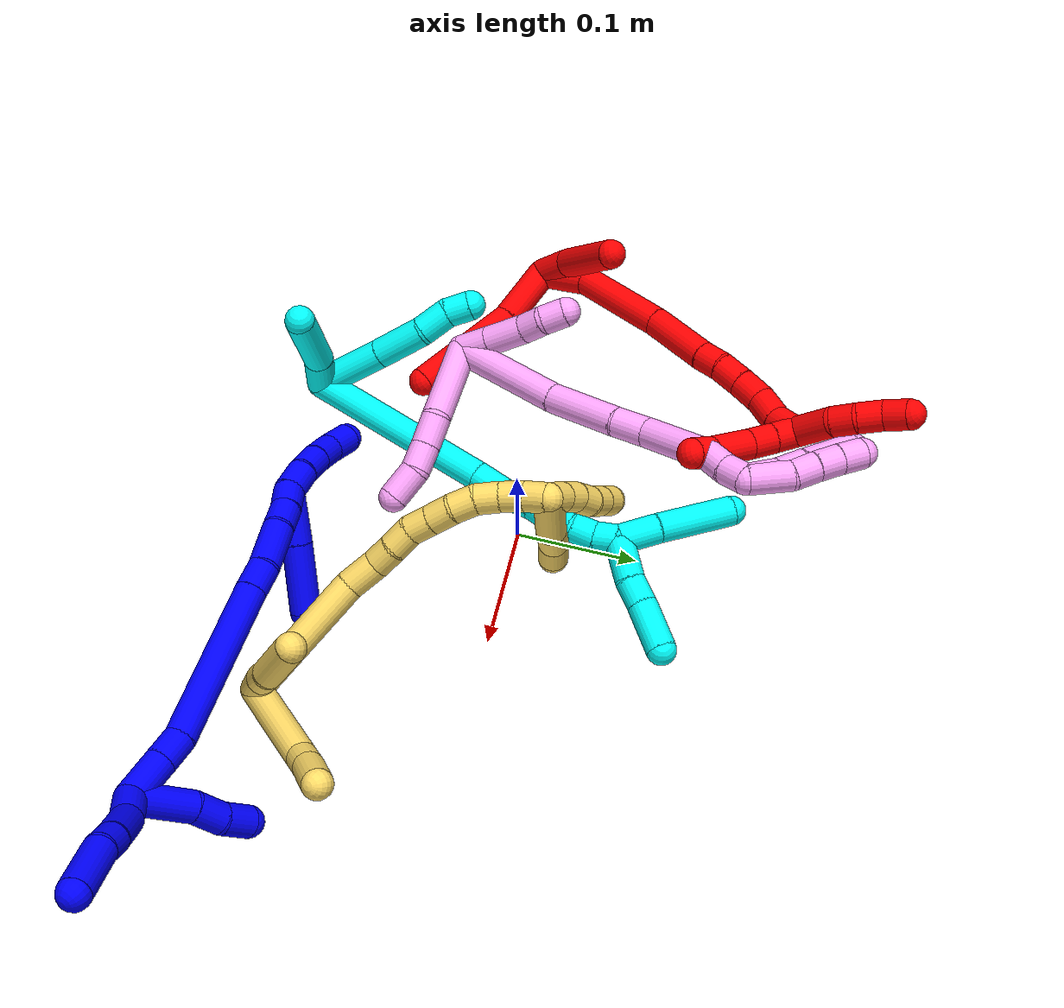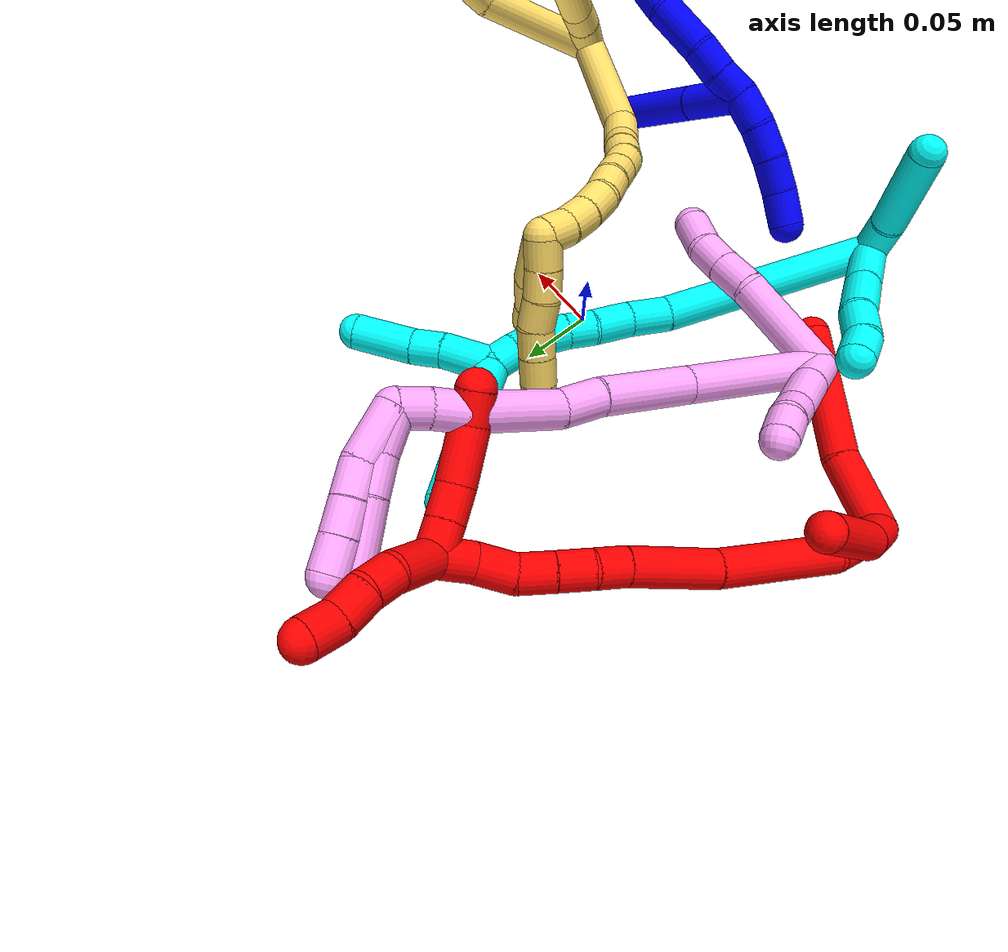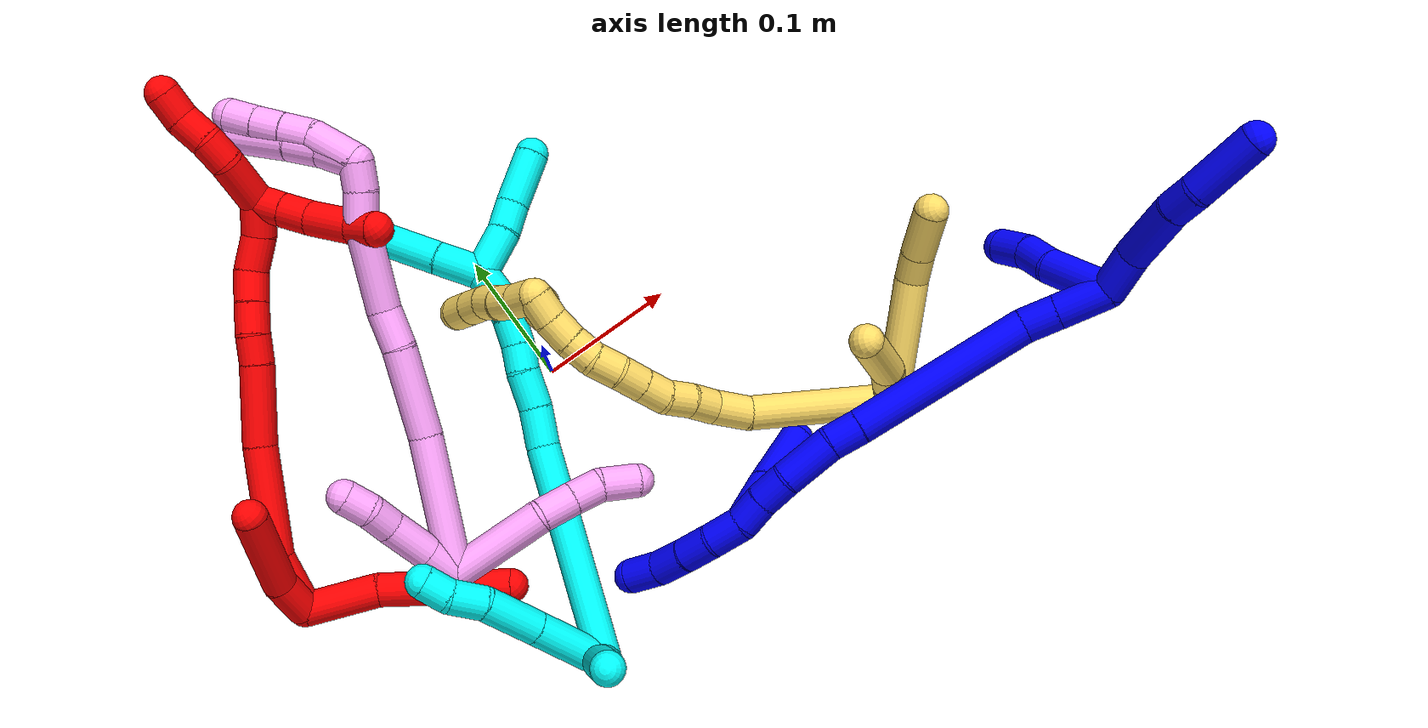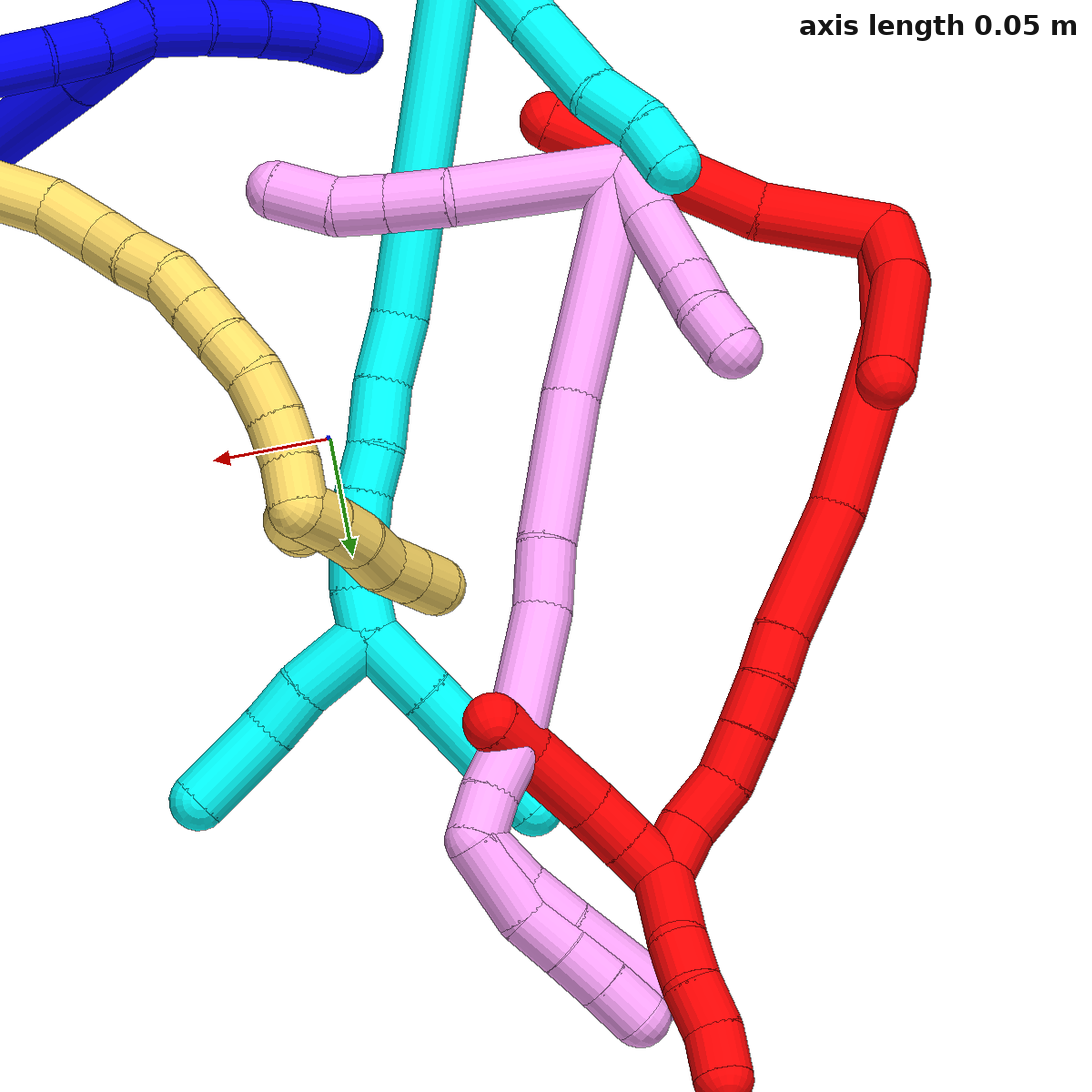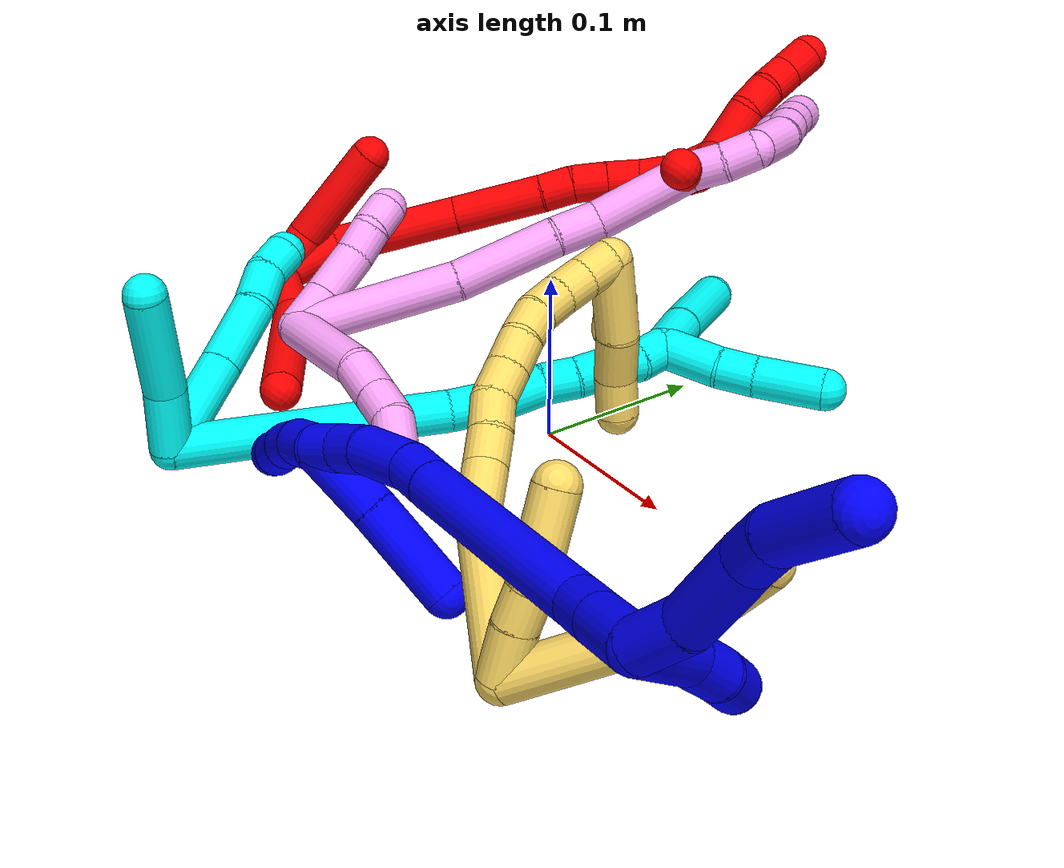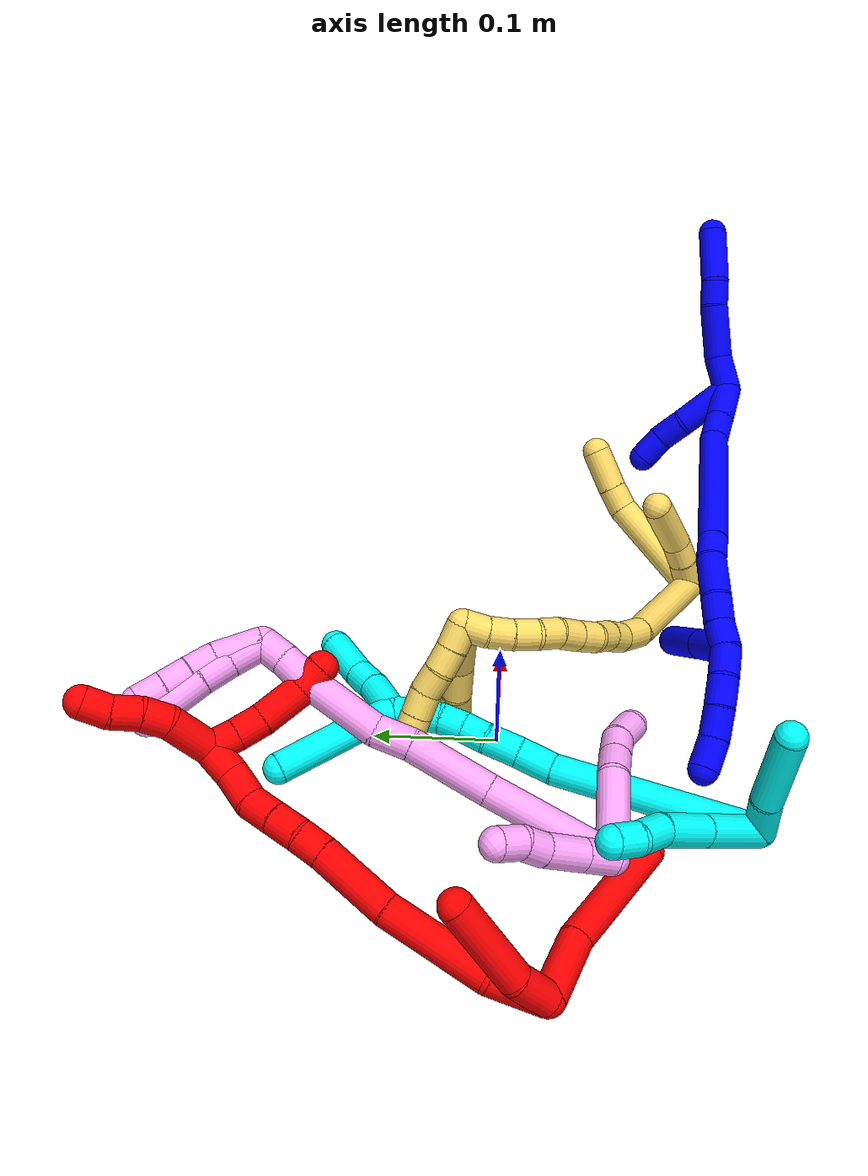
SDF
<sdf version="1.7">
 <world name="default">
  <plugin name="TubeGeneratorPlugin" filename="libtube_generator_plugin.so"/>
  <model name="photoneo_s_sensor">
   <static>1</static>
   <pose>0 0 2 1.57079 1.57079 3.14159</pose>
   <link name="link">
    <inertial><mass>0.1</mass></inertial>
    <sensor name="sensor" type="depth">
     <update_rate>30</update_rate>
     <camera>
      <horizontal_fov>1.22</horizontal_fov>
      <image><width>1920</width><height>1200</height><format>B8G8R8</format></image>
      <clip><near>0.1</near><far>4</far></clip>
      <depth_camera><output>points</output></depth_camera>
     </camera>
     <plugin name="camera_plugin" filename="libgazebo_ros_depth_camera.so">
      <baseline>0.2</baseline>
      <alwaysOn>1</alwaysOn>
      <updateRate>0.0</updateRate>
      <cameraName>camera_ir</cameraName>
      <imageTopicName>/camera/color/image_raw</imageTopicName>
      <cameraInfoTopicName>/camera/color/camera_info</cameraInfoTopicName>
      <depthImageTopicName>/camera/depth/image_raw</depthImageTopicName>
      <depthImageCameraInfoTopicName>/camera/depth/camera_info</depthImageCameraInfoTopicName>
      <pointCloudTopicName>/camera/depth/points</pointCloudTopicName>
      <frameName>fr_optical</frameName>
      <pointCloudCutoff>0.1</pointCloudCutoff>
      <pointCloudCutoffMax>2.0</pointCloudCutoffMax>
      <distortionK1>0</distortionK1>
      <distortionK2>0</distortionK2>
      <distortionK3>0</distortionK3>
      <distortionT1>0</distortionT1>
      <distortionT2>0</distortionT2>
      <CxPrime>0</CxPrime>
      <Cx>0</Cx>
      <Cy>0</Cy>
      <focalLength>0</focalLength>
      <hackBaseline>0</hackBaseline>
     </plugin>
    </sensor>
   </link>
  </model>
  <gravity>0 0 -9.8</gravity>
  <magnetic_field>6e-06 2.3e-05 -4.2e-05</magnetic_field>
  <atmosphere type="adiabatic"/>
  <physics name="default_physics" default="0" type="ode">
   <max_step_size>0.003</max_step_size>
   <real_time_factor>1</real_time_factor>
   <real_time_update_rate>1000</real_time_update_rate>
   <max_contacts>10000</max_contacts>
   <ode>
    <solver>
     <type>quick</type>
     <iters>100</iters>
     <sor>1.3</sor>
     <use_dynamic_moi_rescaling>0</use_dynamic_moi_rescaling>
    </solver>
    <constraints>
     <contact_max_correcting_vel>0</contact_max_correcting_vel>
     <contact_surface_layer>0.001</contact_surface_layer>
     <cfm>0</cfm>
     <erp>0.2</erp>
    </constraints>
   </ode>
  </physics>
  <scene><ambient>0.4 0.4 0.4 1</ambient><background>0.7 0.7 0.7 1</background><shadows>0</shadows></scene>
  <audio><device>default</device></audio>
  <spherical_coordinates>
   <surface_model>EARTH_WGS84</surface_model>
   <latitude_deg>0</latitude_deg>
   <longitude_deg>0</longitude_deg>
   <elevation>0</elevation>
   <heading_deg>0</heading_deg>
  </spherical_coordinates>
  <model name="bin">
   <static>1</static>
   <link name="bottom">
    <collision name="collision-bottom">
     <pose>0 0 -0.01 0 -0 0</pose>
     <geometry><box><size>0.8 0.6 0.02</size></box></geometry>
     <surface>
      <friction><ode><mu>100</mu><mu2>100</mu2></ode></friction>
      <contact><collide_bitmask>65535</collide_bitmask></contact>
     </surface>
    </collision>
   </link>
   <link name="west_wall">
    <collision name="collision-west_wall">
     <pose>-0.41 0 0.1 0 -0 0</pose>
     <geometry><box><size>0.02 0.6 0.2</size></box></geometry>
     <surface>
      <friction><ode><mu>100</mu><mu2>100</mu2></ode></friction>
      <contact><collide_bitmask>65535</collide_bitmask></contact>
     </surface>
    </collision>
   </link>
   <link name="east_wall">
    <collision name="collision-east_wall">
     <pose>0.41 0 0.1 0 -0 0</pose>
     <geometry><box><size>0.02 0.6 0.2</size></box></geometry>
     <surface>
      <friction><ode><mu>100</mu><mu2>100</mu2></ode></friction>
      <contact><collide_bitmask>65535</collide_bitmask></contact>
     </surface>
    </collision>
   </link>
   <link name="south_wall">
    <collision name="collision-south_wall">
     <pose>0 -0.31 0.1 0 -0 0</pose>
     <geometry><box><size>0.8 0.02 0.2</size></box></geometry>
     <surface>
      <friction><ode><mu>100</mu><mu2>100</mu2></ode></friction>
      <contact><collide_bitmask>65535</collide_bitmask></contact>
     </surface>
    </collision>
   </link>
   <link name="north_wall">
    <collision name="collision-north_wall">
     <pose>0 0.31 0.1 0 -0 0</pose>
     <geometry><box><size>0.8 0.02 0.2</size></box></geometry>
     <surface>
      <friction><ode><mu>100</mu><mu2>100</mu2></ode></friction>
      <contact><collide_bitmask>65535</collide_bitmask></contact>
     </surface>
    </collision>
   </link>
  </model>
  <model name="1">
   <static>0</static>
   <link name="1">
    <collision name="collision-cylinder-e_1_2_8">
     <pose>0.00552 0.008896 0.011631 -0.652964 0.360482 -0.123242</pose>
     <geometry><cylinder><radius>0.0125</radius><length>0.031298</length></cylinder></geometry>
     <surface>
      <friction><ode><mu>1.16</mu><mu2>1.16</mu2><slip1>0</slip1><slip2>0</slip2></ode></friction>
      <contact><ode><kp>1e+06</kp><kd>1</kd><max_vel>0</max_vel><min_depth>0.001</min_depth></ode></contact>
     </surface>
    </collision>
    <visual name="visual-cylinder-e_1_2_8">
     <pose>0.00552 0.008896 0.011631 -0.652964 0.360482 -0.123242</pose>
     <geometry><cylinder><radius>0.0125</radius><length>0.031298</length></cylinder></geometry>
     <material><ambient>0 0 1 1</ambient></material>
    </visual>
    <collision name="collision-cylinder-e_2_8_9">
     <pose>0.013737 0.035 0.039932 -0.80126 0.112116 -0.047526</pose>
     <geometry><cylinder><radius>0.0125</radius><length>0.048217</length></cylinder></geometry>
     <surface>
      <friction><ode><mu>1.16</mu><mu2>1.16</mu2><slip1>0</slip1><slip2>0</slip2></ode></friction>
      <contact><ode><kp>1e+06</kp><kd>1</kd><max_vel>0</max_vel><min_depth>0.001</min_depth></ode></contact>
     </surface>
    </collision>
    <visual name="visual-cylinder-e_2_8_9">
     <pose>0.013737 0.035 0.039932 -0.80126 0.112116 -0.047526</pose>
     <geometry><cylinder><radius>0.0125</radius><length>0.048217</length></cylinder></geometry>
     <material><ambient>0 0 1 1</ambient></material>
    </visual>
    <collision name="collision-cylinder-e_3_9_10">
     <pose>0.016838 0.058824 0.065361 -0.646944 0.036785 -0.012333</pose>
     <geometry><cylinder><radius>0.0125</radius><length>0.021971</length></cylinder></geometry>
     <surface>
      <friction><ode><mu>1.16</mu><mu2>1.16</mu2><slip1>0</slip1><slip2>0</slip2></ode></friction>
      <contact><ode><kp>1e+06</kp><kd>1</kd><max_vel>0</max_vel><min_depth>0.001</min_depth></ode></contact>
     </surface>
    </collision>
    <visual name="visual-cylinder-e_3_9_10">
     <pose>0.016838 0.058824 0.065361 -0.646944 0.036785 -0.012333</pose>
     <geometry><cylinder><radius>0.0125</radius><length>0.021971</length></cylinder></geometry>
     <material><ambient>0 0 1 1</ambient></material>
    </visual>
    <collision name="collision-cylinder-e_4_10_6">
     <pose>0.022238 0.075545 0.0956 -0.439681 0.207446 -0.046513</pose>
     <geometry><cylinder><radius>0.0125</radius><length>0.048513</length></cylinder></geometry>
     <surface>
      <friction><ode><mu>1.16</mu><mu2>1.16</mu2><slip1>0</slip1><slip2>0</slip2></ode></friction>
      <contact><ode><kp>1e+06</kp><kd>1</kd><max_vel>0</max_vel><min_depth>0.001</min_depth></ode></contact>
     </surface>
    </collision>
    <visual name="visual-cylinder-e_4_10_6">
     <pose>0.022238 0.075545 0.0956 -0.439681 0.207446 -0.046513</pose>
     <geometry><cylinder><radius>0.0125</radius><length>0.048513</length></cylinder></geometry>
     <material><ambient>0 0 1 1</ambient></material>
    </visual>
    <collision name="collision-cylinder-e_1_2_11">
     <pose>0.018045 -0.005121 -0.016479 2.8403 0.80775 2.45902</pose>
     <geometry><cylinder><radius>0.0125</radius><length>0.049936</length></cylinder></geometry>
     <surface>
      <friction><ode><mu>1.16</mu><mu2>1.16</mu2><slip1>0</slip1><slip2>0</slip2></ode></friction>
      <contact><ode><kp>1e+06</kp><kd>1</kd><max_vel>0</max_vel><min_depth>0.001</min_depth></ode></contact>
     </surface>
    </collision>
    <visual name="visual-cylinder-e_1_2_11">
     <pose>0.018045 -0.005121 -0.016479 2.8403 0.80775 2.45902</pose>
     <geometry><cylinder><radius>0.0125</radius><length>0.049936</length></cylinder></geometry>
     <material><ambient>0 0 1 1</ambient></material>
    </visual>
    <collision name="collision-cylinder-e_2_11_12">
     <pose>0.046071 -0.014602 -0.039133 2.52673 0.922546 2.00469</pose>
     <geometry><cylinder><radius>0.0125</radius><length>0.025039</length></cylinder></geometry>
     <surface>
      <friction><ode><mu>1.16</mu><mu2>1.16</mu2><slip1>0</slip1><slip2>0</slip2></ode></friction>
      <contact><ode><kp>1e+06</kp><kd>1</kd><max_vel>0</max_vel><min_depth>0.001</min_depth></ode></contact>
     </surface>
    </collision>
    <visual name="visual-cylinder-e_2_11_12">
     <pose>0.046071 -0.014602 -0.039133 2.52673 0.922546 2.00469</pose>
     <geometry><cylinder><radius>0.0125</radius><length>0.025039</length></cylinder></geometry>
     <material><ambient>0 0 1 1</ambient></material>
    </visual>
    <collision name="collision-cylinder-e_3_12_5">
     <pose>0.063845 -0.023451 -0.054005 2.66516 0.67255 1.92729</pose>
     <geometry><cylinder><radius>0.0125</radius><length>0.025024</length></cylinder></geometry>
     <surface>
      <friction><ode><mu>1.16</mu><mu2>1.16</mu2><slip1>0</slip1><slip2>0</slip2></ode></friction>
      <contact><ode><kp>1e+06</kp><kd>1</kd><max_vel>0</max_vel><min_depth>0.001</min_depth></ode></contact>
     </surface>
    </collision>
    <visual name="visual-cylinder-e_3_12_5">
     <pose>0.063845 -0.023451 -0.054005 2.66516 0.67255 1.92729</pose>
     <geometry><cylinder><radius>0.0125</radius><length>0.025024</length></cylinder></geometry>
     <material><ambient>0 0 1 1</ambient></material>
    </visual>
    <collision name="collision-cylinder-e_1_2_13">
     <pose>-0.00162 0.000156 -0.018289 -3.13304 -0.088319 2.94857</pose>
     <geometry><cylinder><radius>0.0125</radius><length>0.036723</length></cylinder></geometry>
     <surface>
      <friction><ode><mu>1.16</mu><mu2>1.16</mu2><slip1>0</slip1><slip2>0</slip2></ode></friction>
      <contact><ode><kp>1e+06</kp><kd>1</kd><max_vel>0</max_vel><min_depth>0.001</min_depth></ode></contact>
     </surface>
    </collision>
    <visual name="visual-cylinder-e_1_2_13">
     <pose>-0.00162 0.000156 -0.018289 -3.13304 -0.088319 2.94857</pose>
     <geometry><cylinder><radius>0.0125</radius><length>0.036723</length></cylinder></geometry>
     <material><ambient>0 0 1 1</ambient></material>
    </visual>
    <collision name="collision-cylinder-e_2_13_14">
     <pose>-0.004312 0.0006 -0.048919 -3.1183 -0.086736 2.61711</pose>
     <geometry><cylinder><radius>0.0125</radius><length>0.024782</length></cylinder></geometry>
     <surface>
      <friction><ode><mu>1.16</mu><mu2>1.16</mu2><slip1>0</slip1><slip2>0</slip2></ode></friction>
      <contact><ode><kp>1e+06</kp><kd>1</kd><max_vel>0</max_vel><min_depth>0.001</min_depth></ode></contact>
     </surface>
    </collision>
    <visual name="visual-cylinder-e_2_13_14">
     <pose>-0.004312 0.0006 -0.048919 -3.1183 -0.086736 2.61711</pose>
     <geometry><cylinder><radius>0.0125</radius><length>0.024782</length></cylinder></geometry>
     <material><ambient>0 0 1 1</ambient></material>
    </visual>
    <collision name="collision-cylinder-e_3_14_15">
     <pose>-0.025537 0.010279 -0.123118 -2.99093 -0.311587 2.2457</pose>
     <geometry><cylinder><radius>0.0125</radius><length>0.131463</length></cylinder></geometry>
     <surface>
      <friction><ode><mu>1.16</mu><mu2>1.16</mu2><slip1>0</slip1><slip2>0</slip2></ode></friction>
      <contact><ode><kp>1e+06</kp><kd>1</kd><max_vel>0</max_vel><min_depth>0.001</min_depth></ode></contact>
     </surface>
    </collision>
    <visual name="visual-cylinder-e_3_14_15">
     <pose>-0.025537 0.010279 -0.123118 -2.99093 -0.311587 2.2457</pose>
     <geometry><cylinder><radius>0.0125</radius><length>0.131463</length></cylinder></geometry>
     <material><ambient>0 0 1 1</ambient></material>
    </visual>
    <collision name="collision-cylinder-e_4_15_16">
     <pose>-0.048694 0.021284 -0.196024 -2.99647 -0.262979 2.13647</pose>
     <geometry><cylinder><radius>0.0125</radius><length>0.023127</length></cylinder></geometry>
     <surface>
      <friction><ode><mu>1.16</mu><mu2>1.16</mu2><slip1>0</slip1><slip2>0</slip2></ode></friction>
      <contact><ode><kp>1e+06</kp><kd>1</kd><max_vel>0</max_vel><min_depth>0.001</min_depth></ode></contact>
     </surface>
    </collision>
    <visual name="visual-cylinder-e_4_15_16">
     <pose>-0.048694 0.021284 -0.196024 -2.99647 -0.262979 2.13647</pose>
     <geometry><cylinder><radius>0.0125</radius><length>0.023127</length></cylinder></geometry>
     <material><ambient>0 0 1 1</ambient></material>
    </visual>
    <collision name="collision-cylinder-e_5_16_17">
     <pose>-0.05902 0.022557 -0.225115 3.12263 -0.385333 -3.04445</pose>
     <geometry><cylinder><radius>0.0125</radius><length>0.038947</length></cylinder></geometry>
     <surface>
      <friction><ode><mu>1.16</mu><mu2>1.16</mu2><slip1>0</slip1><slip2>0</slip2></ode></friction>
      <contact><ode><kp>1e+06</kp><kd>1</kd><max_vel>0</max_vel><min_depth>0.001</min_depth></ode></contact>
     </surface>
    </collision>
    <visual name="visual-cylinder-e_5_16_17">
     <pose>-0.05902 0.022557 -0.225115 3.12263 -0.385333 -3.04445</pose>
     <geometry><cylinder><radius>0.0125</radius><length>0.038947</length></cylinder></geometry>
     <material><ambient>0 0 1 1</ambient></material>
    </visual>
    <collision name="collision-cylinder-e_6_17_18">
     <pose>-0.070234 0.019977 -0.253871 2.93571 -0.341873 -2.063</pose>
     <geometry><cylinder><radius>0.0125</radius><length>0.023235</length></cylinder></geometry>
     <surface>
      <friction><ode><mu>1.16</mu><mu2>1.16</mu2><slip1>0</slip1><slip2>0</slip2></ode></friction>
      <contact><ode><kp>1e+06</kp><kd>1</kd><max_vel>0</max_vel><min_depth>0.001</min_depth></ode></contact>
     </surface>
    </collision>
    <visual name="visual-cylinder-e_6_17_18">
     <pose>-0.070234 0.019977 -0.253871 2.93571 -0.341873 -2.063</pose>
     <geometry><cylinder><radius>0.0125</radius><length>0.023235</length></cylinder></geometry>
     <material><ambient>0 0 1 1</ambient></material>
    </visual>
    <collision name="collision-cylinder-e_7_18_1">
     <pose>-0.079026 0.015331 -0.273976 2.89048 -0.467764 -2.16718</pose>
     <geometry><cylinder><radius>0.0125</radius><length>0.021723</length></cylinder></geometry>
     <surface>
      <friction><ode><mu>1.16</mu><mu2>1.16</mu2><slip1>0</slip1><slip2>0</slip2></ode></friction>
      <contact><ode><kp>1e+06</kp><kd>1</kd><max_vel>0</max_vel><min_depth>0.001</min_depth></ode></contact>
     </surface>
    </collision>
    <visual name="visual-cylinder-e_7_18_1">
     <pose>-0.079026 0.015331 -0.273976 2.89048 -0.467764 -2.16718</pose>
     <geometry><cylinder><radius>0.0125</radius><length>0.021723</length></cylinder></geometry>
     <material><ambient>0 0 1 1</ambient></material>
    </visual>
    <collision name="collision-cylinder-e_1_1_19">
     <pose>-0.068269 0.000717 -0.275588 1.00332 0.824601 0.470863</pose>
     <geometry><cylinder><radius>0.0125</radius><length>0.042641</length></cylinder></geometry>
     <surface>
      <friction><ode><mu>1.16</mu><mu2>1.16</mu2><slip1>0</slip1><slip2>0</slip2></ode></friction>
      <contact><ode><kp>1e+06</kp><kd>1</kd><max_vel>0</max_vel><min_depth>0.001</min_depth></ode></contact>
     </surface>
    </collision>
    <visual name="visual-cylinder-e_1_1_19">
     <pose>-0.068269 0.000717 -0.275588 1.00332 0.824601 0.470863</pose>
     <geometry><cylinder><radius>0.0125</radius><length>0.042641</length></cylinder></geometry>
     <material><ambient>0 0 1 1</ambient></material>
    </visual>
    <collision name="collision-cylinder-e_2_19_4">
     <pose>-0.032353 -0.028892 -0.257361 1.03018 0.784443 0.46002</pose>
     <geometry><cylinder><radius>0.0125</radius><length>0.057359</length></cylinder></geometry>
     <surface>
      <friction><ode><mu>1.16</mu><mu2>1.16</mu2><slip1>0</slip1><slip2>0</slip2></ode></friction>
      <contact><ode><kp>1e+06</kp><kd>1</kd><max_vel>0</max_vel><min_depth>0.001</min_depth></ode></contact>
     </surface>
    </collision>
    <visual name="visual-cylinder-e_2_19_4">
     <pose>-0.032353 -0.028892 -0.257361 1.03018 0.784443 0.46002</pose>
     <geometry><cylinder><radius>0.0125</radius><length>0.057359</length></cylinder></geometry>
     <material><ambient>0 0 1 1</ambient></material>
    </visual>
    <collision name="collision-cylinder-e_1_1_20">
     <pose>-0.086213 0.011591 -0.29579 3.03493 -0.181175 -2.07896</pose>
     <geometry><cylinder><radius>0.0125</radius><length>0.025404</length></cylinder></geometry>
     <surface>
      <friction><ode><mu>1.16</mu><mu2>1.16</mu2><slip1>0</slip1><slip2>0</slip2></ode></friction>
      <contact><ode><kp>1e+06</kp><kd>1</kd><max_vel>0</max_vel><min_depth>0.001</min_depth></ode></contact>
     </surface>
    </collision>
    <visual name="visual-cylinder-e_1_1_20">
     <pose>-0.086213 0.011591 -0.29579 3.03493 -0.181175 -2.07896</pose>
     <geometry><cylinder><radius>0.0125</radius><length>0.025404</length></cylinder></geometry>
     <material><ambient>0 0 1 1</ambient></material>
    </visual>
    <collision name="collision-cylinder-e_2_20_21">
     <pose>-0.08945 0.006953 -0.319935 2.86655 -0.077708 -0.547669</pose>
     <geometry><cylinder><radius>0.0125</radius><length>0.024433</length></cylinder></geometry>
     <surface>
      <friction><ode><mu>1.16</mu><mu2>1.16</mu2><slip1>0</slip1><slip2>0</slip2></ode></friction>
      <contact><ode><kp>1e+06</kp><kd>1</kd><max_vel>0</max_vel><min_depth>0.001</min_depth></ode></contact>
     </surface>
    </collision>
    <visual name="visual-cylinder-e_2_20_21">
     <pose>-0.08945 0.006953 -0.319935 2.86655 -0.077708 -0.547669</pose>
     <geometry><cylinder><radius>0.0125</radius><length>0.024433</length></cylinder></geometry>
     <material><ambient>0 0 1 1</ambient></material>
    </visual>
    <collision name="collision-cylinder-e_3_21_22">
     <pose>-0.090494 -0.000739 -0.343508 2.78724 -0.007553 -0.042177</pose>
     <geometry><cylinder><radius>0.0125</radius><length>0.025273</length></cylinder></geometry>
     <surface>
      <friction><ode><mu>1.16</mu><mu2>1.16</mu2><slip1>0</slip1><slip2>0</slip2></ode></friction>
      <contact><ode><kp>1e+06</kp><kd>1</kd><max_vel>0</max_vel><min_depth>0.001</min_depth></ode></contact>
     </surface>
    </collision>
    <visual name="visual-cylinder-e_3_21_22">
     <pose>-0.090494 -0.000739 -0.343508 2.78724 -0.007553 -0.042177</pose>
     <geometry><cylinder><radius>0.0125</radius><length>0.025273</length></cylinder></geometry>
     <material><ambient>0 0 1 1</ambient></material>
    </visual>
    <collision name="collision-cylinder-e_4_22_3">
     <pose>-0.089363 -0.007573 -0.367499 2.94253 0.098638 0.918109</pose>
     <geometry><cylinder><radius>0.0125</radius><length>0.02489</length></cylinder></geometry>
     <surface>
      <friction><ode><mu>1.16</mu><mu2>1.16</mu2><slip1>0</slip1><slip2>0</slip2></ode></friction>
      <contact><ode><kp>1e+06</kp><kd>1</kd><max_vel>0</max_vel><min_depth>0.001</min_depth></ode></contact>
     </surface>
    </collision>
    <visual name="visual-cylinder-e_4_22_3">
     <pose>-0.089363 -0.007573 -0.367499 2.94253 0.098638 0.918109</pose>
     <geometry><cylinder><radius>0.0125</radius><length>0.02489</length></cylinder></geometry>
     <material><ambient>0 0 1 1</ambient></material>
    </visual>
    <collision name="collision-sphere-3">
     <pose>-0.088138 -0.010022 -0.379639 0 -0 0</pose>
     <geometry><sphere><radius>0.0125</radius></sphere></geometry>
     <surface>
      <friction><ode><mu>1.16</mu><mu2>1.16</mu2><slip1>0</slip1><slip2>0</slip2></ode></friction>
      <contact><ode><kp>1e+06</kp><kd>1</kd><max_vel>0</max_vel><min_depth>0.001</min_depth></ode></contact>
     </surface>
    </collision>
    <visual name="visual-sphere-3">
     <pose>-0.088138 -0.010022 -0.379639 0 -0 0</pose>
     <geometry><sphere><radius>0.0125</radius></sphere></geometry>
     <material><ambient>0 0 1 1</ambient></material>
    </visual>
    <collision name="collision-sphere-22">
     <pose>-0.090589 -0.005123 -0.355359 0 -0 0</pose>
     <geometry><sphere><radius>0.0125</radius></sphere></geometry>
     <surface>
      <friction><ode><mu>1.16</mu><mu2>1.16</mu2><slip1>0</slip1><slip2>0</slip2></ode></friction>
      <contact><ode><kp>1e+06</kp><kd>1</kd><max_vel>0</max_vel><min_depth>0.001</min_depth></ode></contact>
     </surface>
    </collision>
    <visual name="visual-sphere-22">
     <pose>-0.090589 -0.005123 -0.355359 0 -0 0</pose>
     <geometry><sphere><radius>0.0125</radius></sphere></geometry>
     <material><ambient>0 0 1 1</ambient></material>
    </visual>
    <collision name="collision-sphere-21">
     <pose>-0.090398 0.003646 -0.331657 0 -0 0</pose>
     <geometry><sphere><radius>0.0125</radius></sphere></geometry>
     <surface>
      <friction><ode><mu>1.16</mu><mu2>1.16</mu2><slip1>0</slip1><slip2>0</slip2></ode></friction>
      <contact><ode><kp>1e+06</kp><kd>1</kd><max_vel>0</max_vel><min_depth>0.001</min_depth></ode></contact>
     </surface>
    </collision>
    <visual name="visual-sphere-21">
     <pose>-0.090398 0.003646 -0.331657 0 -0 0</pose>
     <geometry><sphere><radius>0.0125</radius></sphere></geometry>
     <material><ambient>0 0 1 1</ambient></material>
    </visual>
    <collision name="collision-sphere-20">
     <pose>-0.088501 0.010261 -0.308213 0 -0 0</pose>
     <geometry><sphere><radius>0.0125</radius></sphere></geometry>
     <surface>
      <friction><ode><mu>1.16</mu><mu2>1.16</mu2><slip1>0</slip1><slip2>0</slip2></ode></friction>
      <contact><ode><kp>1e+06</kp><kd>1</kd><max_vel>0</max_vel><min_depth>0.001</min_depth></ode></contact>
     </surface>
    </collision>
    <visual name="visual-sphere-20">
     <pose>-0.088501 0.010261 -0.308213 0 -0 0</pose>
     <geometry><sphere><radius>0.0125</radius></sphere></geometry>
     <material><ambient>0 0 1 1</ambient></material>
    </visual>
    <collision name="collision-sphere-4">
     <pose>-0.012093 -0.046296 -0.246914 0 -0 0</pose>
     <geometry><sphere><radius>0.0125</radius></sphere></geometry>
     <surface>
      <friction><ode><mu>1.16</mu><mu2>1.16</mu2><slip1>0</slip1><slip2>0</slip2></ode></friction>
      <contact><ode><kp>1e+06</kp><kd>1</kd><max_vel>0</max_vel><min_depth>0.001</min_depth></ode></contact>
     </surface>
    </collision>
    <visual name="visual-sphere-4">
     <pose>-0.012093 -0.046296 -0.246914 0 -0 0</pose>
     <geometry><sphere><radius>0.0125</radius></sphere></geometry>
     <material><ambient>0 0 1 1</ambient></material>
    </visual>
    <collision name="collision-sphere-11">
     <pose>0.036091 -0.010242 -0.032958 0 -0 0</pose>
     <geometry><sphere><radius>0.0125</radius></sphere></geometry>
     <surface>
      <friction><ode><mu>1.16</mu><mu2>1.16</mu2><slip1>0</slip1><slip2>0</slip2></ode></friction>
      <contact><ode><kp>1e+06</kp><kd>1</kd><max_vel>0</max_vel><min_depth>0.001</min_depth></ode></contact>
     </surface>
    </collision>
    <visual name="visual-sphere-11">
     <pose>0.036091 -0.010242 -0.032958 0 -0 0</pose>
     <geometry><sphere><radius>0.0125</radius></sphere></geometry>
     <material><ambient>0 0 1 1</ambient></material>
    </visual>
    <collision name="collision-sphere-6">
     <pose>0.027234 0.085648 0.117078 0 -0 0</pose>
     <geometry><sphere><radius>0.0125</radius></sphere></geometry>
     <surface>
      <friction><ode><mu>1.16</mu><mu2>1.16</mu2><slip1>0</slip1><slip2>0</slip2></ode></friction>
      <contact><ode><kp>1e+06</kp><kd>1</kd><max_vel>0</max_vel><min_depth>0.001</min_depth></ode></contact>
     </surface>
    </collision>
    <visual name="visual-sphere-6">
     <pose>0.027234 0.085648 0.117078 0 -0 0</pose>
     <geometry><sphere><radius>0.0125</radius></sphere></geometry>
     <material><ambient>0 0 1 1</ambient></material>
    </visual>
    <collision name="collision-sphere-10">
     <pose>0.017242 0.065441 0.074121 0 -0 0</pose>
     <geometry><sphere><radius>0.0125</radius></sphere></geometry>
     <surface>
      <friction><ode><mu>1.16</mu><mu2>1.16</mu2><slip1>0</slip1><slip2>0</slip2></ode></friction>
      <contact><ode><kp>1e+06</kp><kd>1</kd><max_vel>0</max_vel><min_depth>0.001</min_depth></ode></contact>
     </surface>
    </collision>
    <visual name="visual-sphere-10">
     <pose>0.017242 0.065441 0.074121 0 -0 0</pose>
     <geometry><sphere><radius>0.0125</radius></sphere></geometry>
     <material><ambient>0 0 1 1</ambient></material>
    </visual>
    <collision name="collision-sphere-9">
     <pose>0.016434 0.052207 0.056601 0 -0 0</pose>
     <geometry><sphere><radius>0.0125</radius></sphere></geometry>
     <surface>
      <friction><ode><mu>1.16</mu><mu2>1.16</mu2><slip1>0</slip1><slip2>0</slip2></ode></friction>
      <contact><ode><kp>1e+06</kp><kd>1</kd><max_vel>0</max_vel><min_depth>0.001</min_depth></ode></contact>
     </surface>
    </collision>
    <visual name="visual-sphere-9">
     <pose>0.016434 0.052207 0.056601 0 -0 0</pose>
     <geometry><sphere><radius>0.0125</radius></sphere></geometry>
     <material><ambient>0 0 1 1</ambient></material>
    </visual>
    <collision name="collision-sphere-2">
     <geometry><sphere><radius>0.0125</radius></sphere></geometry>
     <surface>
      <friction><ode><mu>1.16</mu><mu2>1.16</mu2><slip1>0</slip1><slip2>0</slip2></ode></friction>
      <contact><ode><kp>1e+06</kp><kd>1</kd><max_vel>0</max_vel><min_depth>0.001</min_depth></ode></contact>
     </surface>
    </collision>
    <visual name="visual-sphere-2">
     <geometry><sphere><radius>0.0125</radius></sphere></geometry>
     <material><ambient>0 0 1 1</ambient></material>
    </visual>
    <collision name="collision-sphere-19">
     <pose>-0.052614 -0.011488 -0.267808 0 -0 0</pose>
     <geometry><sphere><radius>0.0125</radius></sphere></geometry>
     <surface>
      <friction><ode><mu>1.16</mu><mu2>1.16</mu2><slip1>0</slip1><slip2>0</slip2></ode></friction>
      <contact><ode><kp>1e+06</kp><kd>1</kd><max_vel>0</max_vel><min_depth>0.001</min_depth></ode></contact>
     </surface>
    </collision>
    <visual name="visual-sphere-19">
     <pose>-0.052614 -0.011488 -0.267808 0 -0 0</pose>
     <geometry><sphere><radius>0.0125</radius></sphere></geometry>
     <material><ambient>0 0 1 1</ambient></material>
    </visual>
    <collision name="collision-sphere-8">
     <pose>0.01104 0.017793 0.023262 0 -0 0</pose>
     <geometry><sphere><radius>0.0125</radius></sphere></geometry>
     <surface>
      <friction><ode><mu>1.16</mu><mu2>1.16</mu2><slip1>0</slip1><slip2>0</slip2></ode></friction>
      <contact><ode><kp>1e+06</kp><kd>1</kd><max_vel>0</max_vel><min_depth>0.001</min_depth></ode></contact>
     </surface>
    </collision>
    <visual name="visual-sphere-8">
     <pose>0.01104 0.017793 0.023262 0 -0 0</pose>
     <geometry><sphere><radius>0.0125</radius></sphere></geometry>
     <material><ambient>0 0 1 1</ambient></material>
    </visual>
    <collision name="collision-sphere-12">
     <pose>0.056051 -0.018963 -0.045307 0 -0 0</pose>
     <geometry><sphere><radius>0.0125</radius></sphere></geometry>
     <surface>
      <friction><ode><mu>1.16</mu><mu2>1.16</mu2><slip1>0</slip1><slip2>0</slip2></ode></friction>
      <contact><ode><kp>1e+06</kp><kd>1</kd><max_vel>0</max_vel><min_depth>0.001</min_depth></ode></contact>
     </surface>
    </collision>
    <visual name="visual-sphere-12">
     <pose>0.056051 -0.018963 -0.045307 0 -0 0</pose>
     <geometry><sphere><radius>0.0125</radius></sphere></geometry>
     <material><ambient>0 0 1 1</ambient></material>
    </visual>
    <collision name="collision-sphere-5">
     <pose>0.07164 -0.02794 -0.062702 0 -0 0</pose>
     <geometry><sphere><radius>0.0125</radius></sphere></geometry>
     <surface>
      <friction><ode><mu>1.16</mu><mu2>1.16</mu2><slip1>0</slip1><slip2>0</slip2></ode></friction>
      <contact><ode><kp>1e+06</kp><kd>1</kd><max_vel>0</max_vel><min_depth>0.001</min_depth></ode></contact>
     </surface>
    </collision>
    <visual name="visual-sphere-5">
     <pose>0.07164 -0.02794 -0.062702 0 -0 0</pose>
     <geometry><sphere><radius>0.0125</radius></sphere></geometry>
     <material><ambient>0 0 1 1</ambient></material>
    </visual>
    <collision name="collision-sphere-13">
     <pose>-0.003239 0.000313 -0.036578 0 -0 0</pose>
     <geometry><sphere><radius>0.0125</radius></sphere></geometry>
     <surface>
      <friction><ode><mu>1.16</mu><mu2>1.16</mu2><slip1>0</slip1><slip2>0</slip2></ode></friction>
      <contact><ode><kp>1e+06</kp><kd>1</kd><max_vel>0</max_vel><min_depth>0.001</min_depth></ode></contact>
     </surface>
    </collision>
    <visual name="visual-sphere-13">
     <pose>-0.003239 0.000313 -0.036578 0 -0 0</pose>
     <geometry><sphere><radius>0.0125</radius></sphere></geometry>
     <material><ambient>0 0 1 1</ambient></material>
    </visual>
    <collision name="collision-sphere-14">
     <pose>-0.005386 0.000888 -0.06126 0 -0 0</pose>
     <geometry><sphere><radius>0.0125</radius></sphere></geometry>
     <surface>
      <friction><ode><mu>1.16</mu><mu2>1.16</mu2><slip1>0</slip1><slip2>0</slip2></ode></friction>
      <contact><ode><kp>1e+06</kp><kd>1</kd><max_vel>0</max_vel><min_depth>0.001</min_depth></ode></contact>
     </surface>
    </collision>
    <visual name="visual-sphere-14">
     <pose>-0.005386 0.000888 -0.06126 0 -0 0</pose>
     <geometry><sphere><radius>0.0125</radius></sphere></geometry>
     <material><ambient>0 0 1 1</ambient></material>
    </visual>
    <collision name="collision-sphere-15">
     <pose>-0.045688 0.01967 -0.184975 0 -0 0</pose>
     <geometry><sphere><radius>0.0125</radius></sphere></geometry>
     <surface>
      <friction><ode><mu>1.16</mu><mu2>1.16</mu2><slip1>0</slip1><slip2>0</slip2></ode></friction>
      <contact><ode><kp>1e+06</kp><kd>1</kd><max_vel>0</max_vel><min_depth>0.001</min_depth></ode></contact>
     </surface>
    </collision>
    <visual name="visual-sphere-15">
     <pose>-0.045688 0.01967 -0.184975 0 -0 0</pose>
     <geometry><sphere><radius>0.0125</radius></sphere></geometry>
     <material><ambient>0 0 1 1</ambient></material>
    </visual>
    <collision name="collision-sphere-16">
     <pose>-0.0517 0.022899 -0.207072 0 -0 0</pose>
     <geometry><sphere><radius>0.0125</radius></sphere></geometry>
     <surface>
      <friction><ode><mu>1.16</mu><mu2>1.16</mu2><slip1>0</slip1><slip2>0</slip2></ode></friction>
      <contact><ode><kp>1e+06</kp><kd>1</kd><max_vel>0</max_vel><min_depth>0.001</min_depth></ode></contact>
     </surface>
    </collision>
    <visual name="visual-sphere-16">
     <pose>-0.0517 0.022899 -0.207072 0 -0 0</pose>
     <geometry><sphere><radius>0.0125</radius></sphere></geometry>
     <material><ambient>0 0 1 1</ambient></material>
    </visual>
    <collision name="collision-sphere-17">
     <pose>-0.066339 0.022215 -0.243157 0 -0 0</pose>
     <geometry><sphere><radius>0.0125</radius></sphere></geometry>
     <surface>
      <friction><ode><mu>1.16</mu><mu2>1.16</mu2><slip1>0</slip1><slip2>0</slip2></ode></friction>
      <contact><ode><kp>1e+06</kp><kd>1</kd><max_vel>0</max_vel><min_depth>0.001</min_depth></ode></contact>
     </surface>
    </collision>
    <visual name="visual-sphere-17">
     <pose>-0.066339 0.022215 -0.243157 0 -0 0</pose>
     <geometry><sphere><radius>0.0125</radius></sphere></geometry>
     <material><ambient>0 0 1 1</ambient></material>
    </visual>
    <collision name="collision-sphere-18">
     <pose>-0.074129 0.01774 -0.264585 0 -0 0</pose>
     <geometry><sphere><radius>0.0125</radius></sphere></geometry>
     <surface>
      <friction><ode><mu>1.16</mu><mu2>1.16</mu2><slip1>0</slip1><slip2>0</slip2></ode></friction>
      <contact><ode><kp>1e+06</kp><kd>1</kd><max_vel>0</max_vel><min_depth>0.001</min_depth></ode></contact>
     </surface>
    </collision>
    <visual name="visual-sphere-18">
     <pose>-0.074129 0.01774 -0.264585 0 -0 0</pose>
     <geometry><sphere><radius>0.0125</radius></sphere></geometry>
     <material><ambient>0 0 1 1</ambient></material>
    </visual>
    <collision name="collision-sphere-1">
     <pose>-0.083924 0.012921 -0.283367 0 -0 0</pose>
     <geometry><sphere><radius>0.0125</radius></sphere></geometry>
     <surface>
      <friction><ode><mu>1.16</mu><mu2>1.16</mu2><slip1>0</slip1><slip2>0</slip2></ode></friction>
      <contact><ode><kp>1e+06</kp><kd>1</kd><max_vel>0</max_vel><min_depth>0.001</min_depth></ode></contact>
     </surface>
    </collision>
    <visual name="visual-sphere-1">
     <pose>-0.083924 0.012921 -0.283367 0 -0 0</pose>
     <geometry><sphere><radius>0.0125</radius></sphere></geometry>
     <material><ambient>0 0 1 1</ambient></material>
    </visual>
    <inertial>
     <pose>-0.024019 0.010514 -0.130246 0 -0 0</pose>
     <mass>0.75</mass>
     <inertia>
      <ixx>7.4e-05</ixx>
      <ixy>0</ixy>
      <ixz>0</ixz>
      <iyy>0.000353</iyy>
      <iyz>0</iyz>
      <izz>-1.5e-05</izz>
     </inertia>
    </inertial>
   </link>
   <pose>0.331203 -0.2001 0.129969 1.23194 0.258395 1.13646</pose>
  </model>
  <model name="2">
   <static>0</static>
   <link name="2">
    <collision name="collision-cylinder-e_1_2_8">
     <pose>0.025591 -0.002785 -0.008449 2.8232 1.23622 2.69745</pose>
     <geometry><cylinder><radius>0.0125</radius><length>0.054187</length></cylinder></geometry>
     <surface>
      <friction><ode><mu>1.16</mu><mu2>1.16</mu2><slip1>0</slip1><slip2>0</slip2></ode></friction>
      <contact><ode><kp>1e+06</kp><kd>1</kd><max_vel>0</max_vel><min_depth>0.001</min_depth></ode></contact>
     </surface>
    </collision>
    <visual name="visual-cylinder-e_1_2_8">
     <pose>0.025591 -0.002785 -0.008449 2.8232 1.23622 2.69745</pose>
     <geometry><cylinder><radius>0.0125</radius><length>0.054187</length></cylinder></geometry>
     <material><ambient>1 0 0 1</ambient></material>
    </visual>
    <collision name="collision-cylinder-e_2_8_6">
     <pose>0.092259 -0.019977 -0.036902 2.51741 1.03028 2.1056</pose>
     <geometry><cylinder><radius>0.0125</radius><length>0.095813</length></cylinder></geometry>
     <surface>
      <friction><ode><mu>1.16</mu><mu2>1.16</mu2><slip1>0</slip1><slip2>0</slip2></ode></friction>
      <contact><ode><kp>1e+06</kp><kd>1</kd><max_vel>0</max_vel><min_depth>0.001</min_depth></ode></contact>
     </surface>
    </collision>
    <visual name="visual-cylinder-e_2_8_6">
     <pose>0.092259 -0.019977 -0.036902 2.51741 1.03028 2.1056</pose>
     <geometry><cylinder><radius>0.0125</radius><length>0.095813</length></cylinder></geometry>
     <material><ambient>1 0 0 1</ambient></material>
    </visual>
    <collision name="collision-cylinder-e_1_2_9">
     <pose>-6.9e-05 -1.4e-05 0.015917 0.000895 -0.004314 -2e-06</pose>
     <geometry><cylinder><radius>0.0125</radius><length>0.031834</length></cylinder></geometry>
     <surface>
      <friction><ode><mu>1.16</mu><mu2>1.16</mu2><slip1>0</slip1><slip2>0</slip2></ode></friction>
      <contact><ode><kp>1e+06</kp><kd>1</kd><max_vel>0</max_vel><min_depth>0.001</min_depth></ode></contact>
     </surface>
    </collision>
    <visual name="visual-cylinder-e_1_2_9">
     <pose>-6.9e-05 -1.4e-05 0.015917 0.000895 -0.004314 -2e-06</pose>
     <geometry><cylinder><radius>0.0125</radius><length>0.031834</length></cylinder></geometry>
     <material><ambient>1 0 0 1</ambient></material>
    </visual>
    <collision name="collision-cylinder-e_2_9_5">
     <pose>0.009538 -0.002953 0.064383 0.08962 0.287839 0.012996</pose>
     <geometry><cylinder><radius>0.0125</radius><length>0.068166</length></cylinder></geometry>
     <surface>
      <friction><ode><mu>1.16</mu><mu2>1.16</mu2><slip1>0</slip1><slip2>0</slip2></ode></friction>
      <contact><ode><kp>1e+06</kp><kd>1</kd><max_vel>0</max_vel><min_depth>0.001</min_depth></ode></contact>
     </surface>
    </collision>
    <visual name="visual-cylinder-e_2_9_5">
     <pose>0.009538 -0.002953 0.064383 0.08962 0.287839 0.012996</pose>
     <geometry><cylinder><radius>0.0125</radius><length>0.068166</length></cylinder></geometry>
     <material><ambient>1 0 0 1</ambient></material>
    </visual>
    <collision name="collision-cylinder-e_1_2_10">
     <pose>0.002523 0.010186 0.018858 -0.495269 0.117182 -0.029658</pose>
     <geometry><cylinder><radius>0.0125</radius><length>0.043162</length></cylinder></geometry>
     <surface>
      <friction><ode><mu>1.16</mu><mu2>1.16</mu2><slip1>0</slip1><slip2>0</slip2></ode></friction>
      <contact><ode><kp>1e+06</kp><kd>1</kd><max_vel>0</max_vel><min_depth>0.001</min_depth></ode></contact>
     </surface>
    </collision>
    <visual name="visual-cylinder-e_1_2_10">
     <pose>0.002523 0.010186 0.018858 -0.495269 0.117182 -0.029658</pose>
     <geometry><cylinder><radius>0.0125</radius><length>0.043162</length></cylinder></geometry>
     <material><ambient>1 0 0 1</ambient></material>
    </visual>
    <collision name="collision-cylinder-e_2_10_11">
     <pose>0.022125 0.04151 0.067871 -0.611347 0.434258 -0.139007</pose>
     <geometry><cylinder><radius>0.0125</radius><length>0.081187</length></cylinder></geometry>
     <surface>
      <friction><ode><mu>1.16</mu><mu2>1.16</mu2><slip1>0</slip1><slip2>0</slip2></ode></friction>
      <contact><ode><kp>1e+06</kp><kd>1</kd><max_vel>0</max_vel><min_depth>0.001</min_depth></ode></contact>
     </surface>
    </collision>
    <visual name="visual-cylinder-e_2_10_11">
     <pose>0.022125 0.04151 0.067871 -0.611347 0.434258 -0.139007</pose>
     <geometry><cylinder><radius>0.0125</radius><length>0.081187</length></cylinder></geometry>
     <material><ambient>1 0 0 1</ambient></material>
    </visual>
    <collision name="collision-cylinder-e_3_11_12">
     <pose>0.054785 0.075486 0.119314 -0.54273 0.559848 -0.159626</pose>
     <geometry><cylinder><radius>0.0125</radius><length>0.058677</length></cylinder></geometry>
     <surface>
      <friction><ode><mu>1.16</mu><mu2>1.16</mu2><slip1>0</slip1><slip2>0</slip2></ode></friction>
      <contact><ode><kp>1e+06</kp><kd>1</kd><max_vel>0</max_vel><min_depth>0.001</min_depth></ode></contact>
     </surface>
    </collision>
    <visual name="visual-cylinder-e_3_11_12">
     <pose>0.054785 0.075486 0.119314 -0.54273 0.559848 -0.159626</pose>
     <geometry><cylinder><radius>0.0125</radius><length>0.058677</length></cylinder></geometry>
     <material><ambient>1 0 0 1</ambient></material>
    </visual>
    <collision name="collision-cylinder-e_4_12_13">
     <pose>0.074956 0.093162 0.14856 -0.546018 0.457926 -0.130323</pose>
     <geometry><cylinder><radius>0.0125</radius><length>0.020766</length></cylinder></geometry>
     <surface>
      <friction><ode><mu>1.16</mu><mu2>1.16</mu2><slip1>0</slip1><slip2>0</slip2></ode></friction>
      <contact><ode><kp>1e+06</kp><kd>1</kd><max_vel>0</max_vel><min_depth>0.001</min_depth></ode></contact>
     </surface>
    </collision>
    <visual name="visual-cylinder-e_4_12_13">
     <pose>0.074956 0.093162 0.14856 -0.546018 0.457926 -0.130323</pose>
     <geometry><cylinder><radius>0.0125</radius><length>0.020766</length></cylinder></geometry>
     <material><ambient>1 0 0 1</ambient></material>
    </visual>
    <collision name="collision-cylinder-e_5_13_14">
     <pose>0.085083 0.104613 0.163797 -0.737794 0.512767 -0.202004</pose>
     <geometry><cylinder><radius>0.0125</radius><length>0.022573</length></cylinder></geometry>
     <surface>
      <friction><ode><mu>1.16</mu><mu2>1.16</mu2><slip1>0</slip1><slip2>0</slip2></ode></friction>
      <contact><ode><kp>1e+06</kp><kd>1</kd><max_vel>0</max_vel><min_depth>0.001</min_depth></ode></contact>
     </surface>
    </collision>
    <visual name="visual-cylinder-e_5_13_14">
     <pose>0.085083 0.104613 0.163797 -0.737794 0.512767 -0.202004</pose>
     <geometry><cylinder><radius>0.0125</radius><length>0.022573</length></cylinder></geometry>
     <material><ambient>1 0 0 1</ambient></material>
    </visual>
    <collision name="collision-cylinder-e_6_14_15">
     <pose>0.096455 0.118226 0.178036 -0.787961 0.533914 -0.226412</pose>
     <geometry><cylinder><radius>0.0125</radius><length>0.022933</length></cylinder></geometry>
     <surface>
      <friction><ode><mu>1.16</mu><mu2>1.16</mu2><slip1>0</slip1><slip2>0</slip2></ode></friction>
      <contact><ode><kp>1e+06</kp><kd>1</kd><max_vel>0</max_vel><min_depth>0.001</min_depth></ode></contact>
     </surface>
    </collision>
    <visual name="visual-cylinder-e_6_14_15">
     <pose>0.096455 0.118226 0.178036 -0.787961 0.533914 -0.226412</pose>
     <geometry><cylinder><radius>0.0125</radius><length>0.022933</length></cylinder></geometry>
     <material><ambient>1 0 0 1</ambient></material>
    </visual>
    <collision name="collision-cylinder-e_7_15_16">
     <pose>0.11182 0.129815 0.192812 -0.531141 0.810463 -0.232307</pose>
     <geometry><cylinder><radius>0.0125</radius><length>0.026303</length></cylinder></geometry>
     <surface>
      <friction><ode><mu>1.16</mu><mu2>1.16</mu2><slip1>0</slip1><slip2>0</slip2></ode></friction>
      <contact><ode><kp>1e+06</kp><kd>1</kd><max_vel>0</max_vel><min_depth>0.001</min_depth></ode></contact>
     </surface>
    </collision>
    <visual name="visual-cylinder-e_7_15_16">
     <pose>0.11182 0.129815 0.192812 -0.531141 0.810463 -0.232307</pose>
     <geometry><cylinder><radius>0.0125</radius><length>0.026303</length></cylinder></geometry>
     <material><ambient>1 0 0 1</ambient></material>
    </visual>
    <collision name="collision-cylinder-e_8_16_1">
     <pose>0.127955 0.137398 0.210438 -0.296065 0.572118 -0.087666</pose>
     <geometry><cylinder><radius>0.0125</radius><length>0.024399</length></cylinder></geometry>
     <surface>
      <friction><ode><mu>1.16</mu><mu2>1.16</mu2><slip1>0</slip1><slip2>0</slip2></ode></friction>
      <contact><ode><kp>1e+06</kp><kd>1</kd><max_vel>0</max_vel><min_depth>0.001</min_depth></ode></contact>
     </surface>
    </collision>
    <visual name="visual-cylinder-e_8_16_1">
     <pose>0.127955 0.137398 0.210438 -0.296065 0.572118 -0.087666</pose>
     <geometry><cylinder><radius>0.0125</radius><length>0.024399</length></cylinder></geometry>
     <material><ambient>1 0 0 1</ambient></material>
    </visual>
    <collision name="collision-cylinder-e_1_1_17">
     <pose>0.134687 0.140388 0.238952 0.000151 0.006774 1e-06</pose>
     <geometry><cylinder><radius>0.0125</radius><length>0.037408</length></cylinder></geometry>
     <surface>
      <friction><ode><mu>1.16</mu><mu2>1.16</mu2><slip1>0</slip1><slip2>0</slip2></ode></friction>
      <contact><ode><kp>1e+06</kp><kd>1</kd><max_vel>0</max_vel><min_depth>0.001</min_depth></ode></contact>
     </surface>
    </collision>
    <visual name="visual-cylinder-e_1_1_17">
     <pose>0.134687 0.140388 0.238952 0.000151 0.006774 1e-06</pose>
     <geometry><cylinder><radius>0.0125</radius><length>0.037408</length></cylinder></geometry>
     <material><ambient>1 0 0 1</ambient></material>
    </visual>
    <collision name="collision-cylinder-e_2_17_18">
     <pose>0.133656 0.143192 0.267281 -0.283806 -0.114971 0.016443</pose>
     <geometry><cylinder><radius>0.0125</radius><length>0.020186</length></cylinder></geometry>
     <surface>
      <friction><ode><mu>1.16</mu><mu2>1.16</mu2><slip1>0</slip1><slip2>0</slip2></ode></friction>
      <contact><ode><kp>1e+06</kp><kd>1</kd><max_vel>0</max_vel><min_depth>0.001</min_depth></ode></contact>
     </surface>
    </collision>
    <visual name="visual-cylinder-e_2_17_18">
     <pose>0.133656 0.143192 0.267281 -0.283806 -0.114971 0.016443</pose>
     <geometry><cylinder><radius>0.0125</radius><length>0.020186</length></cylinder></geometry>
     <material><ambient>1 0 0 1</ambient></material>
    </visual>
    <collision name="collision-cylinder-e_3_18_19">
     <pose>0.129662 0.151056 0.28598 -0.508368 -0.266522 0.069628</pose>
     <geometry><cylinder><radius>0.0125</radius><length>0.021534</length></cylinder></geometry>
     <surface>
      <friction><ode><mu>1.16</mu><mu2>1.16</mu2><slip1>0</slip1><slip2>0</slip2></ode></friction>
      <contact><ode><kp>1e+06</kp><kd>1</kd><max_vel>0</max_vel><min_depth>0.001</min_depth></ode></contact>
     </surface>
    </collision>
    <visual name="visual-cylinder-e_3_18_19">
     <pose>0.129662 0.151056 0.28598 -0.508368 -0.266522 0.069628</pose>
     <geometry><cylinder><radius>0.0125</radius><length>0.021534</length></cylinder></geometry>
     <material><ambient>1 0 0 1</ambient></material>
    </visual>
    <collision name="collision-cylinder-e_4_19_4">
     <pose>0.126597 0.159637 0.304873 -0.344661 -0.02197 0.003824</pose>
     <geometry><cylinder><radius>0.0125</radius><length>0.020872</length></cylinder></geometry>
     <surface>
      <friction><ode><mu>1.16</mu><mu2>1.16</mu2><slip1>0</slip1><slip2>0</slip2></ode></friction>
      <contact><ode><kp>1e+06</kp><kd>1</kd><max_vel>0</max_vel><min_depth>0.001</min_depth></ode></contact>
     </surface>
    </collision>
    <visual name="visual-cylinder-e_4_19_4">
     <pose>0.126597 0.159637 0.304873 -0.344661 -0.02197 0.003824</pose>
     <geometry><cylinder><radius>0.0125</radius><length>0.020872</length></cylinder></geometry>
     <material><ambient>1 0 0 1</ambient></material>
    </visual>
    <collision name="collision-cylinder-e_1_1_20">
     <pose>0.14108 0.134146 0.21499 2.27066 0.67387 1.29072</pose>
     <geometry><cylinder><radius>0.0125</radius><length>0.020895</length></cylinder></geometry>
     <surface>
      <friction><ode><mu>1.16</mu><mu2>1.16</mu2><slip1>0</slip1><slip2>0</slip2></ode></friction>
      <contact><ode><kp>1e+06</kp><kd>1</kd><max_vel>0</max_vel><min_depth>0.001</min_depth></ode></contact>
     </surface>
    </collision>
    <visual name="visual-cylinder-e_1_1_20">
     <pose>0.14108 0.134146 0.21499 2.27066 0.67387 1.29072</pose>
     <geometry><cylinder><radius>0.0125</radius><length>0.020895</length></cylinder></geometry>
     <material><ambient>1 0 0 1</ambient></material>
    </visual>
    <collision name="collision-cylinder-e_2_20_21">
     <pose>0.154533 0.120998 0.204827 2.18852 0.686124 1.21059</pose>
     <geometry><cylinder><radius>0.0125</radius><length>0.021888</length></cylinder></geometry>
     <surface>
      <friction><ode><mu>1.16</mu><mu2>1.16</mu2><slip1>0</slip1><slip2>0</slip2></ode></friction>
      <contact><ode><kp>1e+06</kp><kd>1</kd><max_vel>0</max_vel><min_depth>0.001</min_depth></ode></contact>
     </surface>
    </collision>
    <visual name="visual-cylinder-e_2_20_21">
     <pose>0.154533 0.120998 0.204827 2.18852 0.686124 1.21059</pose>
     <geometry><cylinder><radius>0.0125</radius><length>0.021888</length></cylinder></geometry>
     <material><ambient>1 0 0 1</ambient></material>
    </visual>
    <collision name="collision-cylinder-e_3_21_22">
     <pose>0.17312 0.101644 0.194605 1.97445 0.710695 1.02406</pose>
     <geometry><cylinder><radius>0.0125</radius><length>0.035729</length></cylinder></geometry>
     <surface>
      <friction><ode><mu>1.16</mu><mu2>1.16</mu2><slip1>0</slip1><slip2>0</slip2></ode></friction>
      <contact><ode><kp>1e+06</kp><kd>1</kd><max_vel>0</max_vel><min_depth>0.001</min_depth></ode></contact>
     </surface>
    </collision>
    <visual name="visual-cylinder-e_3_21_22">
     <pose>0.17312 0.101644 0.194605 1.97445 0.710695 1.02406</pose>
     <geometry><cylinder><radius>0.0125</radius><length>0.035729</length></cylinder></geometry>
     <material><ambient>1 0 0 1</ambient></material>
    </visual>
    <collision name="collision-cylinder-e_4_22_3">
     <pose>0.191481 0.080847 0.188388 1.67809 0.674156 0.744101</pose>
     <geometry><cylinder><radius>0.0125</radius><length>0.021488</length></cylinder></geometry>
     <surface>
      <friction><ode><mu>1.16</mu><mu2>1.16</mu2><slip1>0</slip1><slip2>0</slip2></ode></friction>
      <contact><ode><kp>1e+06</kp><kd>1</kd><max_vel>0</max_vel><min_depth>0.001</min_depth></ode></contact>
     </surface>
    </collision>
    <visual name="visual-cylinder-e_4_22_3">
     <pose>0.191481 0.080847 0.188388 1.67809 0.674156 0.744101</pose>
     <geometry><cylinder><radius>0.0125</radius><length>0.021488</length></cylinder></geometry>
     <material><ambient>1 0 0 1</ambient></material>
    </visual>
    <collision name="collision-sphere-3">
     <pose>0.198188 0.072502 0.187489 0 -0 0</pose>
     <geometry><sphere><radius>0.0125</radius></sphere></geometry>
     <surface>
      <friction><ode><mu>1.16</mu><mu2>1.16</mu2><slip1>0</slip1><slip2>0</slip2></ode></friction>
      <contact><ode><kp>1e+06</kp><kd>1</kd><max_vel>0</max_vel><min_depth>0.001</min_depth></ode></contact>
     </surface>
    </collision>
    <visual name="visual-sphere-3">
     <pose>0.198188 0.072502 0.187489 0 -0 0</pose>
     <geometry><sphere><radius>0.0125</radius></sphere></geometry>
     <material><ambient>1 0 0 1</ambient></material>
    </visual>
    <collision name="collision-sphere-22">
     <pose>0.184774 0.089192 0.189287 0 -0 0</pose>
     <geometry><sphere><radius>0.0125</radius></sphere></geometry>
     <surface>
      <friction><ode><mu>1.16</mu><mu2>1.16</mu2><slip1>0</slip1><slip2>0</slip2></ode></friction>
      <contact><ode><kp>1e+06</kp><kd>1</kd><max_vel>0</max_vel><min_depth>0.001</min_depth></ode></contact>
     </surface>
    </collision>
    <visual name="visual-sphere-22">
     <pose>0.184774 0.089192 0.189287 0 -0 0</pose>
     <geometry><sphere><radius>0.0125</radius></sphere></geometry>
     <material><ambient>1 0 0 1</ambient></material>
    </visual>
    <collision name="collision-sphere-21">
     <pose>0.161466 0.114096 0.199923 0 -0 0</pose>
     <geometry><sphere><radius>0.0125</radius></sphere></geometry>
     <surface>
      <friction><ode><mu>1.16</mu><mu2>1.16</mu2><slip1>0</slip1><slip2>0</slip2></ode></friction>
      <contact><ode><kp>1e+06</kp><kd>1</kd><max_vel>0</max_vel><min_depth>0.001</min_depth></ode></contact>
     </surface>
    </collision>
    <visual name="visual-sphere-21">
     <pose>0.161466 0.114096 0.199923 0 -0 0</pose>
     <geometry><sphere><radius>0.0125</radius></sphere></geometry>
     <material><ambient>1 0 0 1</ambient></material>
    </visual>
    <collision name="collision-sphere-20">
     <pose>0.147599 0.127901 0.209731 0 -0 0</pose>
     <geometry><sphere><radius>0.0125</radius></sphere></geometry>
     <surface>
      <friction><ode><mu>1.16</mu><mu2>1.16</mu2><slip1>0</slip1><slip2>0</slip2></ode></friction>
      <contact><ode><kp>1e+06</kp><kd>1</kd><max_vel>0</max_vel><min_depth>0.001</min_depth></ode></contact>
     </surface>
    </collision>
    <visual name="visual-sphere-20">
     <pose>0.147599 0.127901 0.209731 0 -0 0</pose>
     <geometry><sphere><radius>0.0125</radius></sphere></geometry>
     <material><ambient>1 0 0 1</ambient></material>
    </visual>
    <collision name="collision-sphere-4">
     <pose>0.126368 0.163162 0.314692 0 -0 0</pose>
     <geometry><sphere><radius>0.0125</radius></sphere></geometry>
     <surface>
      <friction><ode><mu>1.16</mu><mu2>1.16</mu2><slip1>0</slip1><slip2>0</slip2></ode></friction>
      <contact><ode><kp>1e+06</kp><kd>1</kd><max_vel>0</max_vel><min_depth>0.001</min_depth></ode></contact>
     </surface>
    </collision>
    <visual name="visual-sphere-4">
     <pose>0.126368 0.163162 0.314692 0 -0 0</pose>
     <geometry><sphere><radius>0.0125</radius></sphere></geometry>
     <material><ambient>1 0 0 1</ambient></material>
    </visual>
    <collision name="collision-sphere-10">
     <pose>0.005046 0.020373 0.037715 0 -0 0</pose>
     <geometry><sphere><radius>0.0125</radius></sphere></geometry>
     <surface>
      <friction><ode><mu>1.16</mu><mu2>1.16</mu2><slip1>0</slip1><slip2>0</slip2></ode></friction>
      <contact><ode><kp>1e+06</kp><kd>1</kd><max_vel>0</max_vel><min_depth>0.001</min_depth></ode></contact>
     </surface>
    </collision>
    <visual name="visual-sphere-10">
     <pose>0.005046 0.020373 0.037715 0 -0 0</pose>
     <geometry><sphere><radius>0.0125</radius></sphere></geometry>
     <material><ambient>1 0 0 1</ambient></material>
    </visual>
    <collision name="collision-sphere-5">
     <pose>0.019214 -0.005878 0.096933 0 -0 0</pose>
     <geometry><sphere><radius>0.0125</radius></sphere></geometry>
     <surface>
      <friction><ode><mu>1.16</mu><mu2>1.16</mu2><slip1>0</slip1><slip2>0</slip2></ode></friction>
      <contact><ode><kp>1e+06</kp><kd>1</kd><max_vel>0</max_vel><min_depth>0.001</min_depth></ode></contact>
     </surface>
    </collision>
    <visual name="visual-sphere-5">
     <pose>0.019214 -0.005878 0.096933 0 -0 0</pose>
     <geometry><sphere><radius>0.0125</radius></sphere></geometry>
     <material><ambient>1 0 0 1</ambient></material>
    </visual>
    <collision name="collision-sphere-6">
     <pose>0.133336 -0.034385 -0.056906 0 -0 0</pose>
     <geometry><sphere><radius>0.0125</radius></sphere></geometry>
     <surface>
      <friction><ode><mu>1.16</mu><mu2>1.16</mu2><slip1>0</slip1><slip2>0</slip2></ode></friction>
      <contact><ode><kp>1e+06</kp><kd>1</kd><max_vel>0</max_vel><min_depth>0.001</min_depth></ode></contact>
     </surface>
    </collision>
    <visual name="visual-sphere-6">
     <pose>0.133336 -0.034385 -0.056906 0 -0 0</pose>
     <geometry><sphere><radius>0.0125</radius></sphere></geometry>
     <material><ambient>1 0 0 1</ambient></material>
    </visual>
    <collision name="collision-sphere-9">
     <pose>-0.000137 -2.9e-05 0.031834 0 -0 0</pose>
     <geometry><sphere><radius>0.0125</radius></sphere></geometry>
     <surface>
      <friction><ode><mu>1.16</mu><mu2>1.16</mu2><slip1>0</slip1><slip2>0</slip2></ode></friction>
      <contact><ode><kp>1e+06</kp><kd>1</kd><max_vel>0</max_vel><min_depth>0.001</min_depth></ode></contact>
     </surface>
    </collision>
    <visual name="visual-sphere-9">
     <pose>-0.000137 -2.9e-05 0.031834 0 -0 0</pose>
     <geometry><sphere><radius>0.0125</radius></sphere></geometry>
     <material><ambient>1 0 0 1</ambient></material>
    </visual>
    <collision name="collision-sphere-2">
     <geometry><sphere><radius>0.0125</radius></sphere></geometry>
     <surface>
      <friction><ode><mu>1.16</mu><mu2>1.16</mu2><slip1>0</slip1><slip2>0</slip2></ode></friction>
      <contact><ode><kp>1e+06</kp><kd>1</kd><max_vel>0</max_vel><min_depth>0.001</min_depth></ode></contact>
     </surface>
    </collision>
    <visual name="visual-sphere-2">
     <geometry><sphere><radius>0.0125</radius></sphere></geometry>
     <material><ambient>1 0 0 1</ambient></material>
    </visual>
    <collision name="collision-sphere-19">
     <pose>0.126826 0.156111 0.295053 0 -0 0</pose>
     <geometry><sphere><radius>0.0125</radius></sphere></geometry>
     <surface>
      <friction><ode><mu>1.16</mu><mu2>1.16</mu2><slip1>0</slip1><slip2>0</slip2></ode></friction>
      <contact><ode><kp>1e+06</kp><kd>1</kd><max_vel>0</max_vel><min_depth>0.001</min_depth></ode></contact>
     </surface>
    </collision>
    <visual name="visual-sphere-19">
     <pose>0.126826 0.156111 0.295053 0 -0 0</pose>
     <geometry><sphere><radius>0.0125</radius></sphere></geometry>
     <material><ambient>1 0 0 1</ambient></material>
    </visual>
    <collision name="collision-sphere-8">
     <pose>0.051182 -0.00557 -0.016899 0 -0 0</pose>
     <geometry><sphere><radius>0.0125</radius></sphere></geometry>
     <surface>
      <friction><ode><mu>1.16</mu><mu2>1.16</mu2><slip1>0</slip1><slip2>0</slip2></ode></friction>
      <contact><ode><kp>1e+06</kp><kd>1</kd><max_vel>0</max_vel><min_depth>0.001</min_depth></ode></contact>
     </surface>
    </collision>
    <visual name="visual-sphere-8">
     <pose>0.051182 -0.00557 -0.016899 0 -0 0</pose>
     <geometry><sphere><radius>0.0125</radius></sphere></geometry>
     <material><ambient>1 0 0 1</ambient></material>
    </visual>
    <collision name="collision-sphere-11">
     <pose>0.039205 0.062647 0.098027 0 -0 0</pose>
     <geometry><sphere><radius>0.0125</radius></sphere></geometry>
     <surface>
      <friction><ode><mu>1.16</mu><mu2>1.16</mu2><slip1>0</slip1><slip2>0</slip2></ode></friction>
      <contact><ode><kp>1e+06</kp><kd>1</kd><max_vel>0</max_vel><min_depth>0.001</min_depth></ode></contact>
     </surface>
    </collision>
    <visual name="visual-sphere-11">
     <pose>0.039205 0.062647 0.098027 0 -0 0</pose>
     <geometry><sphere><radius>0.0125</radius></sphere></geometry>
     <material><ambient>1 0 0 1</ambient></material>
    </visual>
    <collision name="collision-sphere-12">
     <pose>0.070365 0.088325 0.140601 0 -0 0</pose>
     <geometry><sphere><radius>0.0125</radius></sphere></geometry>
     <surface>
      <friction><ode><mu>1.16</mu><mu2>1.16</mu2><slip1>0</slip1><slip2>0</slip2></ode></friction>
      <contact><ode><kp>1e+06</kp><kd>1</kd><max_vel>0</max_vel><min_depth>0.001</min_depth></ode></contact>
     </surface>
    </collision>
    <visual name="visual-sphere-12">
     <pose>0.070365 0.088325 0.140601 0 -0 0</pose>
     <geometry><sphere><radius>0.0125</radius></sphere></geometry>
     <material><ambient>1 0 0 1</ambient></material>
    </visual>
    <collision name="collision-sphere-13">
     <pose>0.079546 0.097998 0.156519 0 -0 0</pose>
     <geometry><sphere><radius>0.0125</radius></sphere></geometry>
     <surface>
      <friction><ode><mu>1.16</mu><mu2>1.16</mu2><slip1>0</slip1><slip2>0</slip2></ode></friction>
      <contact><ode><kp>1e+06</kp><kd>1</kd><max_vel>0</max_vel><min_depth>0.001</min_depth></ode></contact>
     </surface>
    </collision>
    <visual name="visual-sphere-13">
     <pose>0.079546 0.097998 0.156519 0 -0 0</pose>
     <geometry><sphere><radius>0.0125</radius></sphere></geometry>
     <material><ambient>1 0 0 1</ambient></material>
    </visual>
    <collision name="collision-sphere-14">
     <pose>0.09062 0.111229 0.171074 0 -0 0</pose>
     <geometry><sphere><radius>0.0125</radius></sphere></geometry>
     <surface>
      <friction><ode><mu>1.16</mu><mu2>1.16</mu2><slip1>0</slip1><slip2>0</slip2></ode></friction>
      <contact><ode><kp>1e+06</kp><kd>1</kd><max_vel>0</max_vel><min_depth>0.001</min_depth></ode></contact>
     </surface>
    </collision>
    <visual name="visual-sphere-14">
     <pose>0.09062 0.111229 0.171074 0 -0 0</pose>
     <geometry><sphere><radius>0.0125</radius></sphere></geometry>
     <material><ambient>1 0 0 1</ambient></material>
    </visual>
    <collision name="collision-sphere-15">
     <pose>0.102291 0.125224 0.184997 0 -0 0</pose>
     <geometry><sphere><radius>0.0125</radius></sphere></geometry>
     <surface>
      <friction><ode><mu>1.16</mu><mu2>1.16</mu2><slip1>0</slip1><slip2>0</slip2></ode></friction>
      <contact><ode><kp>1e+06</kp><kd>1</kd><max_vel>0</max_vel><min_depth>0.001</min_depth></ode></contact>
     </surface>
    </collision>
    <visual name="visual-sphere-15">
     <pose>0.102291 0.125224 0.184997 0 -0 0</pose>
     <geometry><sphere><radius>0.0125</radius></sphere></geometry>
     <material><ambient>1 0 0 1</ambient></material>
    </visual>
    <collision name="collision-sphere-16">
     <pose>0.12135 0.134406 0.200627 0 -0 0</pose>
     <geometry><sphere><radius>0.0125</radius></sphere></geometry>
     <surface>
      <friction><ode><mu>1.16</mu><mu2>1.16</mu2><slip1>0</slip1><slip2>0</slip2></ode></friction>
      <contact><ode><kp>1e+06</kp><kd>1</kd><max_vel>0</max_vel><min_depth>0.001</min_depth></ode></contact>
     </surface>
    </collision>
    <visual name="visual-sphere-16">
     <pose>0.12135 0.134406 0.200627 0 -0 0</pose>
     <geometry><sphere><radius>0.0125</radius></sphere></geometry>
     <material><ambient>1 0 0 1</ambient></material>
    </visual>
    <collision name="collision-sphere-1">
     <pose>0.13456 0.140391 0.220248 0 -0 0</pose>
     <geometry><sphere><radius>0.0125</radius></sphere></geometry>
     <surface>
      <friction><ode><mu>1.16</mu><mu2>1.16</mu2><slip1>0</slip1><slip2>0</slip2></ode></friction>
      <contact><ode><kp>1e+06</kp><kd>1</kd><max_vel>0</max_vel><min_depth>0.001</min_depth></ode></contact>
     </surface>
    </collision>
    <visual name="visual-sphere-1">
     <pose>0.13456 0.140391 0.220248 0 -0 0</pose>
     <geometry><sphere><radius>0.0125</radius></sphere></geometry>
     <material><ambient>1 0 0 1</ambient></material>
    </visual>
    <collision name="collision-sphere-18">
     <pose>0.132498 0.146 0.276907 0 -0 0</pose>
     <geometry><sphere><radius>0.0125</radius></sphere></geometry>
     <surface>
      <friction><ode><mu>1.16</mu><mu2>1.16</mu2><slip1>0</slip1><slip2>0</slip2></ode></friction>
      <contact><ode><kp>1e+06</kp><kd>1</kd><max_vel>0</max_vel><min_depth>0.001</min_depth></ode></contact>
     </surface>
    </collision>
    <visual name="visual-sphere-18">
     <pose>0.132498 0.146 0.276907 0 -0 0</pose>
     <geometry><sphere><radius>0.0125</radius></sphere></geometry>
     <material><ambient>1 0 0 1</ambient></material>
    </visual>
    <collision name="collision-sphere-17">
     <pose>0.134814 0.140385 0.257656 0 -0 0</pose>
     <geometry><sphere><radius>0.0125</radius></sphere></geometry>
     <surface>
      <friction><ode><mu>1.16</mu><mu2>1.16</mu2><slip1>0</slip1><slip2>0</slip2></ode></friction>
      <contact><ode><kp>1e+06</kp><kd>1</kd><max_vel>0</max_vel><min_depth>0.001</min_depth></ode></contact>
     </surface>
    </collision>
    <visual name="visual-sphere-17">
     <pose>0.134814 0.140385 0.257656 0 -0 0</pose>
     <geometry><sphere><radius>0.0125</radius></sphere></geometry>
     <material><ambient>1 0 0 1</ambient></material>
    </visual>
    <inertial>
     <pose>0.07673 0.060391 0.109507 0 -0 0</pose>
     <mass>0.75</mass>
     <inertia>
      <ixx>0.000157</ixx>
      <ixy>0</ixy>
      <ixz>0</ixz>
      <iyy>0.000237</iyy>
      <iyz>0</iyz>
      <izz>-0.000115</izz>
     </inertia>
    </inertial>
   </link>
   <pose>-0.245359 -0.040605 0.015258 -0.771499 -0.105856 -0.064054</pose>
  </model>
  <model name="3">
   <static>0</static>
   <link name="3">
    <collision name="collision-cylinder-e_1_2_8">
     <pose>-0.002727 0.025598 0.015291 -1.03231 -0.091202 0.051778</pose>
     <geometry><cylinder><radius>0.0125</radius><length>0.059883</length></cylinder></geometry>
     <surface>
      <friction><ode><mu>1.16</mu><mu2>1.16</mu2><slip1>0</slip1><slip2>0</slip2></ode></friction>
      <contact><ode><kp>1e+06</kp><kd>1</kd><max_vel>0</max_vel><min_depth>0.001</min_depth></ode></contact>
     </surface>
    </collision>
    <visual name="visual-cylinder-e_1_2_8">
     <pose>-0.002727 0.025598 0.015291 -1.03231 -0.091202 0.051778</pose>
     <geometry><cylinder><radius>0.0125</radius><length>0.059883</length></cylinder></geometry>
     <material><ambient>0.003922 1 0.996078 1</ambient></material>
    </visual>
    <collision name="collision-cylinder-e_2_8_9">
     <pose>-0.007488 0.069385 0.042102 -1.00626 -0.09422 0.051883</pose>
     <geometry><cylinder><radius>0.0125</radius><length>0.043252</length></cylinder></geometry>
     <surface>
      <friction><ode><mu>1.16</mu><mu2>1.16</mu2><slip1>0</slip1><slip2>0</slip2></ode></friction>
      <contact><ode><kp>1e+06</kp><kd>1</kd><max_vel>0</max_vel><min_depth>0.001</min_depth></ode></contact>
     </surface>
    </collision>
    <visual name="visual-cylinder-e_2_8_9">
     <pose>-0.007488 0.069385 0.042102 -1.00626 -0.09422 0.051883</pose>
     <geometry><cylinder><radius>0.0125</radius><length>0.043252</length></cylinder></geometry>
     <material><ambient>0.003922 1 0.996078 1</ambient></material>
    </visual>
    <collision name="collision-cylinder-e_3_9_10">
     <pose>-0.014021 0.098381 0.059378 -1.0813 -0.352073 0.212759</pose>
     <geometry><cylinder><radius>0.0125</radius><length>0.026089</length></cylinder></geometry>
     <surface>
      <friction><ode><mu>1.16</mu><mu2>1.16</mu2><slip1>0</slip1><slip2>0</slip2></ode></friction>
      <contact><ode><kp>1e+06</kp><kd>1</kd><max_vel>0</max_vel><min_depth>0.001</min_depth></ode></contact>
     </surface>
    </collision>
    <visual name="visual-cylinder-e_3_9_10">
     <pose>-0.014021 0.098381 0.059378 -1.0813 -0.352073 0.212759</pose>
     <geometry><cylinder><radius>0.0125</radius><length>0.026089</length></cylinder></geometry>
     <material><ambient>0.003922 1 0.996078 1</ambient></material>
    </visual>
    <collision name="collision-cylinder-e_4_10_6">
     <pose>-0.019207 0.118967 0.068569 -1.23309 -0.066254 0.046963</pose>
     <geometry><cylinder><radius>0.0125</radius><length>0.020776</length></cylinder></geometry>
     <surface>
      <friction><ode><mu>1.16</mu><mu2>1.16</mu2><slip1>0</slip1><slip2>0</slip2></ode></friction>
      <contact><ode><kp>1e+06</kp><kd>1</kd><max_vel>0</max_vel><min_depth>0.001</min_depth></ode></contact>
     </surface>
    </collision>
    <visual name="visual-cylinder-e_4_10_6">
     <pose>-0.019207 0.118967 0.068569 -1.23309 -0.066254 0.046963</pose>
     <geometry><cylinder><radius>0.0125</radius><length>0.020776</length></cylinder></geometry>
     <material><ambient>0.003922 1 0.996078 1</ambient></material>
    </visual>
    <collision name="collision-cylinder-e_1_2_11">
     <pose>0.000801 -0.000438 0.018627 0.023524 0.042954 0.000505</pose>
     <geometry><cylinder><radius>0.0125</radius><length>0.0373</length></cylinder></geometry>
     <surface>
      <friction><ode><mu>1.16</mu><mu2>1.16</mu2><slip1>0</slip1><slip2>0</slip2></ode></friction>
      <contact><ode><kp>1e+06</kp><kd>1</kd><max_vel>0</max_vel><min_depth>0.001</min_depth></ode></contact>
     </surface>
    </collision>
    <visual name="visual-cylinder-e_1_2_11">
     <pose>0.000801 -0.000438 0.018627 0.023524 0.042954 0.000505</pose>
     <geometry><cylinder><radius>0.0125</radius><length>0.0373</length></cylinder></geometry>
     <material><ambient>0.003922 1 0.996078 1</ambient></material>
    </visual>
    <collision name="collision-cylinder-e_2_11_5">
     <pose>0.004762 -0.006905 0.067857 0.194504 0.100995 0.009861</pose>
     <geometry><cylinder><radius>0.0125</radius><length>0.0627</length></cylinder></geometry>
     <surface>
      <friction><ode><mu>1.16</mu><mu2>1.16</mu2><slip1>0</slip1><slip2>0</slip2></ode></friction>
      <contact><ode><kp>1e+06</kp><kd>1</kd><max_vel>0</max_vel><min_depth>0.001</min_depth></ode></contact>
     </surface>
    </collision>
    <visual name="visual-cylinder-e_2_11_5">
     <pose>0.004762 -0.006905 0.067857 0.194504 0.100995 0.009861</pose>
     <geometry><cylinder><radius>0.0125</radius><length>0.0627</length></cylinder></geometry>
     <material><ambient>0.003922 1 0.996078 1</ambient></material>
    </visual>
    <collision name="collision-cylinder-e_1_2_12">
     <pose>0.050503 0.063437 -0.002293 -1.60693 0.672049 -0.694871</pose>
     <geometry><cylinder><radius>0.0125</radius><length>0.162236</length></cylinder></geometry>
     <surface>
      <friction><ode><mu>1.16</mu><mu2>1.16</mu2><slip1>0</slip1><slip2>0</slip2></ode></friction>
      <contact><ode><kp>1e+06</kp><kd>1</kd><max_vel>0</max_vel><min_depth>0.001</min_depth></ode></contact>
     </surface>
    </collision>
    <visual name="visual-cylinder-e_1_2_12">
     <pose>0.050503 0.063437 -0.002293 -1.60693 0.672049 -0.694871</pose>
     <geometry><cylinder><radius>0.0125</radius><length>0.162236</length></cylinder></geometry>
     <material><ambient>0.003922 1 0.996078 1</ambient></material>
    </visual>
    <collision name="collision-cylinder-e_2_12_13">
     <pose>0.111394 0.137322 -0.003049 -1.42461 0.77714 -0.679618</pose>
     <geometry><cylinder><radius>0.0125</radius><length>0.029626</length></cylinder></geometry>
     <surface>
      <friction><ode><mu>1.16</mu><mu2>1.16</mu2><slip1>0</slip1><slip2>0</slip2></ode></friction>
      <contact><ode><kp>1e+06</kp><kd>1</kd><max_vel>0</max_vel><min_depth>0.001</min_depth></ode></contact>
     </surface>
    </collision>
    <visual name="visual-cylinder-e_2_12_13">
     <pose>0.111394 0.137322 -0.003049 -1.42461 0.77714 -0.679618</pose>
     <geometry><cylinder><radius>0.0125</radius><length>0.029626</length></cylinder></geometry>
     <material><ambient>0.003922 1 0.996078 1</ambient></material>
    </visual>
    <collision name="collision-cylinder-e_3_13_14">
     <pose>0.130106 0.15873 0.001325 -1.31769 0.634063 -0.497539</pose>
     <geometry><cylinder><radius>0.0125</radius><length>0.028103</length></cylinder></geometry>
     <surface>
      <friction><ode><mu>1.16</mu><mu2>1.16</mu2><slip1>0</slip1><slip2>0</slip2></ode></friction>
      <contact><ode><kp>1e+06</kp><kd>1</kd><max_vel>0</max_vel><min_depth>0.001</min_depth></ode></contact>
     </surface>
    </collision>
    <visual name="visual-cylinder-e_3_13_14">
     <pose>0.130106 0.15873 0.001325 -1.31769 0.634063 -0.497539</pose>
     <geometry><cylinder><radius>0.0125</radius><length>0.028103</length></cylinder></geometry>
     <material><ambient>0.003922 1 0.996078 1</ambient></material>
    </visual>
    <collision name="collision-cylinder-e_4_14_15">
     <pose>0.145504 0.17672 0.005058 -1.44372 0.784379 -0.69842</pose>
     <geometry><cylinder><radius>0.0125</radius><length>0.020027</length></cylinder></geometry>
     <surface>
      <friction><ode><mu>1.16</mu><mu2>1.16</mu2><slip1>0</slip1><slip2>0</slip2></ode></friction>
      <contact><ode><kp>1e+06</kp><kd>1</kd><max_vel>0</max_vel><min_depth>0.001</min_depth></ode></contact>
     </surface>
    </collision>
    <visual name="visual-cylinder-e_4_14_15">
     <pose>0.145504 0.17672 0.005058 -1.44372 0.784379 -0.69842</pose>
     <geometry><cylinder><radius>0.0125</radius><length>0.020027</length></cylinder></geometry>
     <material><ambient>0.003922 1 0.996078 1</ambient></material>
    </visual>
    <collision name="collision-cylinder-e_5_15_16">
     <pose>0.158589 0.191603 0.007456 -1.38207 0.644782 -0.539113</pose>
     <geometry><cylinder><radius>0.0125</radius><length>0.020004</length></cylinder></geometry>
     <surface>
      <friction><ode><mu>1.16</mu><mu2>1.16</mu2><slip1>0</slip1><slip2>0</slip2></ode></friction>
      <contact><ode><kp>1e+06</kp><kd>1</kd><max_vel>0</max_vel><min_depth>0.001</min_depth></ode></contact>
     </surface>
    </collision>
    <visual name="visual-cylinder-e_5_15_16">
     <pose>0.158589 0.191603 0.007456 -1.38207 0.644782 -0.539113</pose>
     <geometry><cylinder><radius>0.0125</radius><length>0.020004</length></cylinder></geometry>
     <material><ambient>0.003922 1 0.996078 1</ambient></material>
    </visual>
    <collision name="collision-cylinder-e_6_16_17">
     <pose>0.169468 0.208187 0.008681 -1.60223 0.508311 -0.523823</pose>
     <geometry><cylinder><radius>0.0125</radius><length>0.020002</length></cylinder></geometry>
     <surface>
      <friction><ode><mu>1.16</mu><mu2>1.16</mu2><slip1>0</slip1><slip2>0</slip2></ode></friction>
      <contact><ode><kp>1e+06</kp><kd>1</kd><max_vel>0</max_vel><min_depth>0.001</min_depth></ode></contact>
     </surface>
    </collision>
    <visual name="visual-cylinder-e_6_16_17">
     <pose>0.169468 0.208187 0.008681 -1.60223 0.508311 -0.523823</pose>
     <geometry><cylinder><radius>0.0125</radius><length>0.020002</length></cylinder></geometry>
     <material><ambient>0.003922 1 0.996078 1</ambient></material>
    </visual>
    <collision name="collision-cylinder-e_7_17_1">
     <pose>0.177514 0.226243 0.010132 -1.38773 0.323417 -0.269759</pose>
     <geometry><cylinder><radius>0.0125</radius><length>0.020002</length></cylinder></geometry>
     <surface>
      <friction><ode><mu>1.16</mu><mu2>1.16</mu2><slip1>0</slip1><slip2>0</slip2></ode></friction>
      <contact><ode><kp>1e+06</kp><kd>1</kd><max_vel>0</max_vel><min_depth>0.001</min_depth></ode></contact>
     </surface>
    </collision>
    <visual name="visual-cylinder-e_7_17_1">
     <pose>0.177514 0.226243 0.010132 -1.38773 0.323417 -0.269759</pose>
     <geometry><cylinder><radius>0.0125</radius><length>0.020002</length></cylinder></geometry>
     <material><ambient>0.003922 1 0.996078 1</ambient></material>
    </visual>
    <collision name="collision-cylinder-e_1_1_18">
     <pose>0.197844 0.238473 0.007837 -2.51593 1.28922 -2.32893</pose>
     <geometry><cylinder><radius>0.0125</radius><length>0.035711</length></cylinder></geometry>
     <surface>
      <friction><ode><mu>1.16</mu><mu2>1.16</mu2><slip1>0</slip1><slip2>0</slip2></ode></friction>
      <contact><ode><kp>1e+06</kp><kd>1</kd><max_vel>0</max_vel><min_depth>0.001</min_depth></ode></contact>
     </surface>
    </collision>
    <visual name="visual-cylinder-e_1_1_18">
     <pose>0.197844 0.238473 0.007837 -2.51593 1.28922 -2.32893</pose>
     <geometry><cylinder><radius>0.0125</radius><length>0.035711</length></cylinder></geometry>
     <material><ambient>0.003922 1 0.996078 1</ambient></material>
    </visual>
    <collision name="collision-cylinder-e_2_18_19">
     <pose>0.225324 0.245225 0.00163 -2.08748 1.16611 -1.6956</pose>
     <geometry><cylinder><radius>0.0125</radius><length>0.022472</length></cylinder></geometry>
     <surface>
      <friction><ode><mu>1.16</mu><mu2>1.16</mu2><slip1>0</slip1><slip2>0</slip2></ode></friction>
      <contact><ode><kp>1e+06</kp><kd>1</kd><max_vel>0</max_vel><min_depth>0.001</min_depth></ode></contact>
     </surface>
    </collision>
    <visual name="visual-cylinder-e_2_18_19">
     <pose>0.225324 0.245225 0.00163 -2.08748 1.16611 -1.6956</pose>
     <geometry><cylinder><radius>0.0125</radius><length>0.022472</length></cylinder></geometry>
     <material><ambient>0.003922 1 0.996078 1</ambient></material>
    </visual>
    <collision name="collision-cylinder-e_3_19_4">
     <pose>0.25572 0.25459 -0.002568 -1.9204 1.28603 -1.639</pose>
     <geometry><cylinder><radius>0.0125</radius><length>0.041818</length></cylinder></geometry>
     <surface>
      <friction><ode><mu>1.16</mu><mu2>1.16</mu2><slip1>0</slip1><slip2>0</slip2></ode></friction>
      <contact><ode><kp>1e+06</kp><kd>1</kd><max_vel>0</max_vel><min_depth>0.001</min_depth></ode></contact>
     </surface>
    </collision>
    <visual name="visual-cylinder-e_3_19_4">
     <pose>0.25572 0.25459 -0.002568 -1.9204 1.28603 -1.639</pose>
     <geometry><cylinder><radius>0.0125</radius><length>0.041818</length></cylinder></geometry>
     <material><ambient>0.003922 1 0.996078 1</ambient></material>
    </visual>
    <collision name="collision-cylinder-e_1_1_20">
     <pose>0.176347 0.252047 0.01169 -1.58105 -0.257757 0.260384</pose>
     <geometry><cylinder><radius>0.0125</radius><length>0.034087</length></cylinder></geometry>
     <surface>
      <friction><ode><mu>1.16</mu><mu2>1.16</mu2><slip1>0</slip1><slip2>0</slip2></ode></friction>
      <contact><ode><kp>1e+06</kp><kd>1</kd><max_vel>0</max_vel><min_depth>0.001</min_depth></ode></contact>
     </surface>
    </collision>
    <visual name="visual-cylinder-e_1_1_20">
     <pose>0.176347 0.252047 0.01169 -1.58105 -0.257757 0.260384</pose>
     <geometry><cylinder><radius>0.0125</radius><length>0.034087</length></cylinder></geometry>
     <material><ambient>0.003922 1 0.996078 1</ambient></material>
    </visual>
    <collision name="collision-cylinder-e_2_20_3">
     <pose>0.164061 0.300423 0.009142 -1.64524 -0.243369 0.261988</pose>
     <geometry><cylinder><radius>0.0125</radius><length>0.065913</length></cylinder></geometry>
     <surface>
      <friction><ode><mu>1.16</mu><mu2>1.16</mu2><slip1>0</slip1><slip2>0</slip2></ode></friction>
      <contact><ode><kp>1e+06</kp><kd>1</kd><max_vel>0</max_vel><min_depth>0.001</min_depth></ode></contact>
     </surface>
    </collision>
    <visual name="visual-cylinder-e_2_20_3">
     <pose>0.164061 0.300423 0.009142 -1.64524 -0.243369 0.261988</pose>
     <geometry><cylinder><radius>0.0125</radius><length>0.065913</length></cylinder></geometry>
     <material><ambient>0.003922 1 0.996078 1</ambient></material>
    </visual>
    <collision name="collision-sphere-3">
     <pose>0.156119 0.33232 0.006763 0 -0 0</pose>
     <geometry><sphere><radius>0.0125</radius></sphere></geometry>
     <surface>
      <friction><ode><mu>1.16</mu><mu2>1.16</mu2><slip1>0</slip1><slip2>0</slip2></ode></friction>
      <contact><ode><kp>1e+06</kp><kd>1</kd><max_vel>0</max_vel><min_depth>0.001</min_depth></ode></contact>
     </surface>
    </collision>
    <visual name="visual-sphere-3">
     <pose>0.156119 0.33232 0.006763 0 -0 0</pose>
     <geometry><sphere><radius>0.0125</radius></sphere></geometry>
     <material><ambient>0.003922 1 0.996078 1</ambient></material>
    </visual>
    <collision name="collision-sphere-20">
     <pose>0.172003 0.268526 0.011521 0 -0 0</pose>
     <geometry><sphere><radius>0.0125</radius></sphere></geometry>
     <surface>
      <friction><ode><mu>1.16</mu><mu2>1.16</mu2><slip1>0</slip1><slip2>0</slip2></ode></friction>
      <contact><ode><kp>1e+06</kp><kd>1</kd><max_vel>0</max_vel><min_depth>0.001</min_depth></ode></contact>
     </surface>
    </collision>
    <visual name="visual-sphere-20">
     <pose>0.172003 0.268526 0.011521 0 -0 0</pose>
     <geometry><sphere><radius>0.0125</radius></sphere></geometry>
     <material><ambient>0.003922 1 0.996078 1</ambient></material>
    </visual>
    <collision name="collision-sphere-4">
     <pose>0.275786 0.260109 -0.00458 0 -0 0</pose>
     <geometry><sphere><radius>0.0125</radius></sphere></geometry>
     <surface>
      <friction><ode><mu>1.16</mu><mu2>1.16</mu2><slip1>0</slip1><slip2>0</slip2></ode></friction>
      <contact><ode><kp>1e+06</kp><kd>1</kd><max_vel>0</max_vel><min_depth>0.001</min_depth></ode></contact>
     </surface>
    </collision>
    <visual name="visual-sphere-4">
     <pose>0.275786 0.260109 -0.00458 0 -0 0</pose>
     <geometry><sphere><radius>0.0125</radius></sphere></geometry>
     <material><ambient>0.003922 1 0.996078 1</ambient></material>
    </visual>
    <collision name="collision-sphere-11">
     <pose>0.001602 -0.000877 0.037255 0 -0 0</pose>
     <geometry><sphere><radius>0.0125</radius></sphere></geometry>
     <surface>
      <friction><ode><mu>1.16</mu><mu2>1.16</mu2><slip1>0</slip1><slip2>0</slip2></ode></friction>
      <contact><ode><kp>1e+06</kp><kd>1</kd><max_vel>0</max_vel><min_depth>0.001</min_depth></ode></contact>
     </surface>
    </collision>
    <visual name="visual-sphere-11">
     <pose>0.001602 -0.000877 0.037255 0 -0 0</pose>
     <geometry><sphere><radius>0.0125</radius></sphere></geometry>
     <material><ambient>0.003922 1 0.996078 1</ambient></material>
    </visual>
    <collision name="collision-sphere-6">
     <pose>-0.019895 0.128746 0.072003 0 -0 0</pose>
     <geometry><sphere><radius>0.0125</radius></sphere></geometry>
     <surface>
      <friction><ode><mu>1.16</mu><mu2>1.16</mu2><slip1>0</slip1><slip2>0</slip2></ode></friction>
      <contact><ode><kp>1e+06</kp><kd>1</kd><max_vel>0</max_vel><min_depth>0.001</min_depth></ode></contact>
     </surface>
    </collision>
    <visual name="visual-sphere-6">
     <pose>-0.019895 0.128746 0.072003 0 -0 0</pose>
     <geometry><sphere><radius>0.0125</radius></sphere></geometry>
     <material><ambient>0.003922 1 0.996078 1</ambient></material>
    </visual>
    <collision name="collision-sphere-10">
     <pose>-0.01852 0.109187 0.065135 0 -0 0</pose>
     <geometry><sphere><radius>0.0125</radius></sphere></geometry>
     <surface>
      <friction><ode><mu>1.16</mu><mu2>1.16</mu2><slip1>0</slip1><slip2>0</slip2></ode></friction>
      <contact><ode><kp>1e+06</kp><kd>1</kd><max_vel>0</max_vel><min_depth>0.001</min_depth></ode></contact>
     </surface>
    </collision>
    <visual name="visual-sphere-10">
     <pose>-0.01852 0.109187 0.065135 0 -0 0</pose>
     <geometry><sphere><radius>0.0125</radius></sphere></geometry>
     <material><ambient>0.003922 1 0.996078 1</ambient></material>
    </visual>
    <collision name="collision-sphere-9">
     <pose>-0.009523 0.087574 0.053621 0 -0 0</pose>
     <geometry><sphere><radius>0.0125</radius></sphere></geometry>
     <surface>
      <friction><ode><mu>1.16</mu><mu2>1.16</mu2><slip1>0</slip1><slip2>0</slip2></ode></friction>
      <contact><ode><kp>1e+06</kp><kd>1</kd><max_vel>0</max_vel><min_depth>0.001</min_depth></ode></contact>
     </surface>
    </collision>
    <visual name="visual-sphere-9">
     <pose>-0.009523 0.087574 0.053621 0 -0 0</pose>
     <geometry><sphere><radius>0.0125</radius></sphere></geometry>
     <material><ambient>0.003922 1 0.996078 1</ambient></material>
    </visual>
    <collision name="collision-sphere-2">
     <geometry><sphere><radius>0.0125</radius></sphere></geometry>
     <surface>
      <friction><ode><mu>1.16</mu><mu2>1.16</mu2><slip1>0</slip1><slip2>0</slip2></ode></friction>
      <contact><ode><kp>1e+06</kp><kd>1</kd><max_vel>0</max_vel><min_depth>0.001</min_depth></ode></contact>
     </surface>
    </collision>
    <visual name="visual-sphere-2">
     <geometry><sphere><radius>0.0125</radius></sphere></geometry>
     <material><ambient>0.003922 1 0.996078 1</ambient></material>
    </visual>
    <collision name="collision-sphere-19">
     <pose>0.235653 0.249072 -0.000556 0 -0 0</pose>
     <geometry><sphere><radius>0.0125</radius></sphere></geometry>
     <surface>
      <friction><ode><mu>1.16</mu><mu2>1.16</mu2><slip1>0</slip1><slip2>0</slip2></ode></friction>
      <contact><ode><kp>1e+06</kp><kd>1</kd><max_vel>0</max_vel><min_depth>0.001</min_depth></ode></contact>
     </surface>
    </collision>
    <visual name="visual-sphere-19">
     <pose>0.235653 0.249072 -0.000556 0 -0 0</pose>
     <geometry><sphere><radius>0.0125</radius></sphere></geometry>
     <material><ambient>0.003922 1 0.996078 1</ambient></material>
    </visual>
    <collision name="collision-sphere-8">
     <pose>-0.005454 0.051195 0.030583 0 -0 0</pose>
     <geometry><sphere><radius>0.0125</radius></sphere></geometry>
     <surface>
      <friction><ode><mu>1.16</mu><mu2>1.16</mu2><slip1>0</slip1><slip2>0</slip2></ode></friction>
      <contact><ode><kp>1e+06</kp><kd>1</kd><max_vel>0</max_vel><min_depth>0.001</min_depth></ode></contact>
     </surface>
    </collision>
    <visual name="visual-sphere-8">
     <pose>-0.005454 0.051195 0.030583 0 -0 0</pose>
     <geometry><sphere><radius>0.0125</radius></sphere></geometry>
     <material><ambient>0.003922 1 0.996078 1</ambient></material>
    </visual>
    <collision name="collision-sphere-5">
     <pose>0.007923 -0.012934 0.09846 0 -0 0</pose>
     <geometry><sphere><radius>0.0125</radius></sphere></geometry>
     <surface>
      <friction><ode><mu>1.16</mu><mu2>1.16</mu2><slip1>0</slip1><slip2>0</slip2></ode></friction>
      <contact><ode><kp>1e+06</kp><kd>1</kd><max_vel>0</max_vel><min_depth>0.001</min_depth></ode></contact>
     </surface>
    </collision>
    <visual name="visual-sphere-5">
     <pose>0.007923 -0.012934 0.09846 0 -0 0</pose>
     <geometry><sphere><radius>0.0125</radius></sphere></geometry>
     <material><ambient>0.003922 1 0.996078 1</ambient></material>
    </visual>
    <collision name="collision-sphere-12">
     <pose>0.101007 0.126875 -0.004587 0 -0 0</pose>
     <geometry><sphere><radius>0.0125</radius></sphere></geometry>
     <surface>
      <friction><ode><mu>1.16</mu><mu2>1.16</mu2><slip1>0</slip1><slip2>0</slip2></ode></friction>
      <contact><ode><kp>1e+06</kp><kd>1</kd><max_vel>0</max_vel><min_depth>0.001</min_depth></ode></contact>
     </surface>
    </collision>
    <visual name="visual-sphere-12">
     <pose>0.101007 0.126875 -0.004587 0 -0 0</pose>
     <geometry><sphere><radius>0.0125</radius></sphere></geometry>
     <material><ambient>0.003922 1 0.996078 1</ambient></material>
    </visual>
    <collision name="collision-sphere-13">
     <pose>0.121782 0.14777 -0.00151 0 -0 0</pose>
     <geometry><sphere><radius>0.0125</radius></sphere></geometry>
     <surface>
      <friction><ode><mu>1.16</mu><mu2>1.16</mu2><slip1>0</slip1><slip2>0</slip2></ode></friction>
      <contact><ode><kp>1e+06</kp><kd>1</kd><max_vel>0</max_vel><min_depth>0.001</min_depth></ode></contact>
     </surface>
    </collision>
    <visual name="visual-sphere-13">
     <pose>0.121782 0.14777 -0.00151 0 -0 0</pose>
     <geometry><sphere><radius>0.0125</radius></sphere></geometry>
     <material><ambient>0.003922 1 0.996078 1</ambient></material>
    </visual>
    <collision name="collision-sphere-14">
     <pose>0.138431 0.16969 0.004159 0 -0 0</pose>
     <geometry><sphere><radius>0.0125</radius></sphere></geometry>
     <surface>
      <friction><ode><mu>1.16</mu><mu2>1.16</mu2><slip1>0</slip1><slip2>0</slip2></ode></friction>
      <contact><ode><kp>1e+06</kp><kd>1</kd><max_vel>0</max_vel><min_depth>0.001</min_depth></ode></contact>
     </surface>
    </collision>
    <visual name="visual-sphere-14">
     <pose>0.138431 0.16969 0.004159 0 -0 0</pose>
     <geometry><sphere><radius>0.0125</radius></sphere></geometry>
     <material><ambient>0.003922 1 0.996078 1</ambient></material>
    </visual>
    <collision name="collision-sphere-15">
     <pose>0.152577 0.183751 0.005956 0 -0 0</pose>
     <geometry><sphere><radius>0.0125</radius></sphere></geometry>
     <surface>
      <friction><ode><mu>1.16</mu><mu2>1.16</mu2><slip1>0</slip1><slip2>0</slip2></ode></friction>
      <contact><ode><kp>1e+06</kp><kd>1</kd><max_vel>0</max_vel><min_depth>0.001</min_depth></ode></contact>
     </surface>
    </collision>
    <visual name="visual-sphere-15">
     <pose>0.152577 0.183751 0.005956 0 -0 0</pose>
     <geometry><sphere><radius>0.0125</radius></sphere></geometry>
     <material><ambient>0.003922 1 0.996078 1</ambient></material>
    </visual>
    <collision name="collision-sphere-16">
     <pose>0.1646 0.199455 0.008955 0 -0 0</pose>
     <geometry><sphere><radius>0.0125</radius></sphere></geometry>
     <surface>
      <friction><ode><mu>1.16</mu><mu2>1.16</mu2><slip1>0</slip1><slip2>0</slip2></ode></friction>
      <contact><ode><kp>1e+06</kp><kd>1</kd><max_vel>0</max_vel><min_depth>0.001</min_depth></ode></contact>
     </surface>
    </collision>
    <visual name="visual-sphere-16">
     <pose>0.1646 0.199455 0.008955 0 -0 0</pose>
     <geometry><sphere><radius>0.0125</radius></sphere></geometry>
     <material><ambient>0.003922 1 0.996078 1</ambient></material>
    </visual>
    <collision name="collision-sphere-17">
     <pose>0.174335 0.216919 0.008406 0 -0 0</pose>
     <geometry><sphere><radius>0.0125</radius></sphere></geometry>
     <surface>
      <friction><ode><mu>1.16</mu><mu2>1.16</mu2><slip1>0</slip1><slip2>0</slip2></ode></friction>
      <contact><ode><kp>1e+06</kp><kd>1</kd><max_vel>0</max_vel><min_depth>0.001</min_depth></ode></contact>
     </surface>
    </collision>
    <visual name="visual-sphere-17">
     <pose>0.174335 0.216919 0.008406 0 -0 0</pose>
     <geometry><sphere><radius>0.0125</radius></sphere></geometry>
     <material><ambient>0.003922 1 0.996078 1</ambient></material>
    </visual>
    <collision name="collision-sphere-1">
     <pose>0.180692 0.235567 0.011859 0 -0 0</pose>
     <geometry><sphere><radius>0.0125</radius></sphere></geometry>
     <surface>
      <friction><ode><mu>1.16</mu><mu2>1.16</mu2><slip1>0</slip1><slip2>0</slip2></ode></friction>
      <contact><ode><kp>1e+06</kp><kd>1</kd><max_vel>0</max_vel><min_depth>0.001</min_depth></ode></contact>
     </surface>
    </collision>
    <visual name="visual-sphere-1">
     <pose>0.180692 0.235567 0.011859 0 -0 0</pose>
     <geometry><sphere><radius>0.0125</radius></sphere></geometry>
     <material><ambient>0.003922 1 0.996078 1</ambient></material>
    </visual>
    <collision name="collision-sphere-18">
     <pose>0.214996 0.241379 0.003815 0 -0 0</pose>
     <geometry><sphere><radius>0.0125</radius></sphere></geometry>
     <surface>
      <friction><ode><mu>1.16</mu><mu2>1.16</mu2><slip1>0</slip1><slip2>0</slip2></ode></friction>
      <contact><ode><kp>1e+06</kp><kd>1</kd><max_vel>0</max_vel><min_depth>0.001</min_depth></ode></contact>
     </surface>
    </collision>
    <visual name="visual-sphere-18">
     <pose>0.214996 0.241379 0.003815 0 -0 0</pose>
     <geometry><sphere><radius>0.0125</radius></sphere></geometry>
     <material><ambient>0.003922 1 0.996078 1</ambient></material>
    </visual>
    <inertial>
     <pose>0.0892 0.129429 0.016095 0 -0 0</pose>
     <mass>0.75</mass>
     <inertia>
      <ixx>0.000153</ixx>
      <ixy>0</ixy>
      <ixz>0</ixz>
      <iyy>5.5e-05</iyy>
      <iyz>0</iyz>
      <izz>-0.000575</izz>
     </inertia>
    </inertial>
   </link>
   <pose>-0.0921 -0.197571 0.012712 -0.04605 -0.095586 0.33935</pose>
  </model>
  <model name="4">
   <static>0</static>
   <link name="4">
    <collision name="collision-cylinder-e_1_2_8">
     <pose>0.027608 -0.004525 0.023167 0.192904 0.863407 0.089086</pose>
     <geometry><cylinder><radius>0.0125</radius><length>0.072647</length></cylinder></geometry>
     <surface>
      <friction><ode><mu>1.16</mu><mu2>1.16</mu2><slip1>0</slip1><slip2>0</slip2></ode></friction>
      <contact><ode><kp>1e+06</kp><kd>1</kd><max_vel>0</max_vel><min_depth>0.001</min_depth></ode></contact>
     </surface>
    </collision>
    <visual name="visual-cylinder-e_1_2_8">
     <pose>0.027608 -0.004525 0.023167 0.192904 0.863407 0.089086</pose>
     <geometry><cylinder><radius>0.0125</radius><length>0.072647</length></cylinder></geometry>
     <material><ambient>1 0.65098 0.996078 1</ambient></material>
    </visual>
    <collision name="collision-cylinder-e_2_8_9">
     <pose>0.064406 -0.014705 0.053964 0.637734 0.768968 0.265585</pose>
     <geometry><cylinder><radius>0.0125</radius><length>0.02643</length></cylinder></geometry>
     <surface>
      <friction><ode><mu>1.16</mu><mu2>1.16</mu2><slip1>0</slip1><slip2>0</slip2></ode></friction>
      <contact><ode><kp>1e+06</kp><kd>1</kd><max_vel>0</max_vel><min_depth>0.001</min_depth></ode></contact>
     </surface>
    </collision>
    <visual name="visual-cylinder-e_2_8_9">
     <pose>0.064406 -0.014705 0.053964 0.637734 0.768968 0.265585</pose>
     <geometry><cylinder><radius>0.0125</radius><length>0.02643</length></cylinder></geometry>
     <material><ambient>1 0.65098 0.996078 1</ambient></material>
    </visual>
    <collision name="collision-cylinder-e_3_9_10">
     <pose>0.081262 -0.024867 0.068547 0.575227 0.746568 0.230681</pose>
     <geometry><cylinder><radius>0.0125</radius><length>0.022578</length></cylinder></geometry>
     <surface>
      <friction><ode><mu>1.16</mu><mu2>1.16</mu2><slip1>0</slip1><slip2>0</slip2></ode></friction>
      <contact><ode><kp>1e+06</kp><kd>1</kd><max_vel>0</max_vel><min_depth>0.001</min_depth></ode></contact>
     </surface>
    </collision>
    <visual name="visual-cylinder-e_3_9_10">
     <pose>0.081262 -0.024867 0.068547 0.575227 0.746568 0.230681</pose>
     <geometry><cylinder><radius>0.0125</radius><length>0.022578</length></cylinder></geometry>
     <material><ambient>1 0.65098 0.996078 1</ambient></material>
    </visual>
    <collision name="collision-cylinder-e_4_10_6">
     <pose>0.094488 -0.03708 0.086016 0.632331 0.403146 0.133502</pose>
     <geometry><cylinder><radius>0.0125</radius><length>0.028346</length></cylinder></geometry>
     <surface>
      <friction><ode><mu>1.16</mu><mu2>1.16</mu2><slip1>0</slip1><slip2>0</slip2></ode></friction>
      <contact><ode><kp>1e+06</kp><kd>1</kd><max_vel>0</max_vel><min_depth>0.001</min_depth></ode></contact>
     </surface>
    </collision>
    <visual name="visual-cylinder-e_4_10_6">
     <pose>0.094488 -0.03708 0.086016 0.632331 0.403146 0.133502</pose>
     <geometry><cylinder><radius>0.0125</radius><length>0.028346</length></cylinder></geometry>
     <material><ambient>1 0.65098 0.996078 1</ambient></material>
    </visual>
    <collision name="collision-cylinder-e_1_2_11">
     <pose>0.004183 0.008668 -0.008824 -2.36516 0.326114 -0.764924</pose>
     <geometry><cylinder><radius>0.0125</radius><length>0.026115</length></cylinder></geometry>
     <surface>
      <friction><ode><mu>1.16</mu><mu2>1.16</mu2><slip1>0</slip1><slip2>0</slip2></ode></friction>
      <contact><ode><kp>1e+06</kp><kd>1</kd><max_vel>0</max_vel><min_depth>0.001</min_depth></ode></contact>
     </surface>
    </collision>
    <visual name="visual-cylinder-e_1_2_11">
     <pose>0.004183 0.008668 -0.008824 -2.36516 0.326114 -0.764924</pose>
     <geometry><cylinder><radius>0.0125</radius><length>0.026115</length></cylinder></geometry>
     <material><ambient>1 0.65098 0.996078 1</ambient></material>
    </visual>
    <collision name="collision-cylinder-e_2_11_12">
     <pose>0.013512 0.028658 -0.028974 -2.35627 0.310888 -0.72344</pose>
     <geometry><cylinder><radius>0.0125</radius><length>0.033642</length></cylinder></geometry>
     <surface>
      <friction><ode><mu>1.16</mu><mu2>1.16</mu2><slip1>0</slip1><slip2>0</slip2></ode></friction>
      <contact><ode><kp>1e+06</kp><kd>1</kd><max_vel>0</max_vel><min_depth>0.001</min_depth></ode></contact>
     </surface>
    </collision>
    <visual name="visual-cylinder-e_2_11_12">
     <pose>0.013512 0.028658 -0.028974 -2.35627 0.310888 -0.72344</pose>
     <geometry><cylinder><radius>0.0125</radius><length>0.033642</length></cylinder></geometry>
     <material><ambient>1 0.65098 0.996078 1</ambient></material>
    </visual>
    <collision name="collision-cylinder-e_3_12_13">
     <pose>0.02175 0.047885 -0.045606 -2.16216 0.314113 -0.577583</pose>
     <geometry><cylinder><radius>0.0125</radius><length>0.020019</length></cylinder></geometry>
     <surface>
      <friction><ode><mu>1.16</mu><mu2>1.16</mu2><slip1>0</slip1><slip2>0</slip2></ode></friction>
      <contact><ode><kp>1e+06</kp><kd>1</kd><max_vel>0</max_vel><min_depth>0.001</min_depth></ode></contact>
     </surface>
    </collision>
    <visual name="visual-cylinder-e_3_12_13">
     <pose>0.02175 0.047885 -0.045606 -2.16216 0.314113 -0.577583</pose>
     <geometry><cylinder><radius>0.0125</radius><length>0.020019</length></cylinder></geometry>
     <material><ambient>1 0.65098 0.996078 1</ambient></material>
    </visual>
    <collision name="collision-cylinder-e_4_13_5">
     <pose>0.026977 0.061761 -0.058788 -2.49265 0.2127 -0.614646</pose>
     <geometry><cylinder><radius>0.0125</radius><length>0.020224</length></cylinder></geometry>
     <surface>
      <friction><ode><mu>1.16</mu><mu2>1.16</mu2><slip1>0</slip1><slip2>0</slip2></ode></friction>
      <contact><ode><kp>1e+06</kp><kd>1</kd><max_vel>0</max_vel><min_depth>0.001</min_depth></ode></contact>
     </surface>
    </collision>
    <visual name="visual-cylinder-e_4_13_5">
     <pose>0.026977 0.061761 -0.058788 -2.49265 0.2127 -0.614646</pose>
     <geometry><cylinder><radius>0.0125</radius><length>0.020224</length></cylinder></geometry>
     <material><ambient>1 0.65098 0.996078 1</ambient></material>
    </visual>
    <collision name="collision-cylinder-e_1_2_14">
     <pose>0.04345 0.01613 -0.01918 -2.44235 1.04763 -2.01551</pose>
     <geometry><cylinder><radius>0.0125</radius><length>0.100318</length></cylinder></geometry>
     <surface>
      <friction><ode><mu>1.16</mu><mu2>1.16</mu2><slip1>0</slip1><slip2>0</slip2></ode></friction>
      <contact><ode><kp>1e+06</kp><kd>1</kd><max_vel>0</max_vel><min_depth>0.001</min_depth></ode></contact>
     </surface>
    </collision>
    <visual name="visual-cylinder-e_1_2_14">
     <pose>0.04345 0.01613 -0.01918 -2.44235 1.04763 -2.01551</pose>
     <geometry><cylinder><radius>0.0125</radius><length>0.100318</length></cylinder></geometry>
     <material><ambient>1 0.65098 0.996078 1</ambient></material>
    </visual>
    <collision name="collision-cylinder-e_2_14_15">
     <pose>0.113315 0.046807 -0.050828 -2.27941 0.943297 -1.674</pose>
     <geometry><cylinder><radius>0.0125</radius><length>0.065264</length></cylinder></geometry>
     <surface>
      <friction><ode><mu>1.16</mu><mu2>1.16</mu2><slip1>0</slip1><slip2>0</slip2></ode></friction>
      <contact><ode><kp>1e+06</kp><kd>1</kd><max_vel>0</max_vel><min_depth>0.001</min_depth></ode></contact>
     </surface>
    </collision>
    <visual name="visual-cylinder-e_2_14_15">
     <pose>0.113315 0.046807 -0.050828 -2.27941 0.943297 -1.674</pose>
     <geometry><cylinder><radius>0.0125</radius><length>0.065264</length></cylinder></geometry>
     <material><ambient>1 0.65098 0.996078 1</ambient></material>
    </visual>
    <collision name="collision-cylinder-e_3_15_16">
     <pose>0.15088 0.066636 -0.070604 -2.51571 0.890761 -1.95021</pose>
     <geometry><cylinder><radius>0.0125</radius><length>0.028679</length></cylinder></geometry>
     <surface>
      <friction><ode><mu>1.16</mu><mu2>1.16</mu2><slip1>0</slip1><slip2>0</slip2></ode></friction>
      <contact><ode><kp>1e+06</kp><kd>1</kd><max_vel>0</max_vel><min_depth>0.001</min_depth></ode></contact>
     </surface>
    </collision>
    <visual name="visual-cylinder-e_3_15_16">
     <pose>0.15088 0.066636 -0.070604 -2.51571 0.890761 -1.95021</pose>
     <geometry><cylinder><radius>0.0125</radius><length>0.028679</length></cylinder></geometry>
     <material><ambient>1 0.65098 0.996078 1</ambient></material>
    </visual>
    <collision name="collision-cylinder-e_4_16_17">
     <pose>0.187232 0.088092 -0.08729 -2.09628 0.932538 -1.43608</pose>
     <geometry><cylinder><radius>0.0125</radius><length>0.062761</length></cylinder></geometry>
     <surface>
      <friction><ode><mu>1.16</mu><mu2>1.16</mu2><slip1>0</slip1><slip2>0</slip2></ode></friction>
      <contact><ode><kp>1e+06</kp><kd>1</kd><max_vel>0</max_vel><min_depth>0.001</min_depth></ode></contact>
     </surface>
    </collision>
    <visual name="visual-cylinder-e_4_16_17">
     <pose>0.187232 0.088092 -0.08729 -2.09628 0.932538 -1.43608</pose>
     <geometry><cylinder><radius>0.0125</radius><length>0.062761</length></cylinder></geometry>
     <material><ambient>1 0.65098 0.996078 1</ambient></material>
    </visual>
    <collision name="collision-cylinder-e_5_17_18">
     <pose>0.222742 0.108098 -0.098331 -1.97997 1.18572 -1.59693</pose>
     <geometry><cylinder><radius>0.0125</radius><length>0.022243</length></cylinder></geometry>
     <surface>
      <friction><ode><mu>1.16</mu><mu2>1.16</mu2><slip1>0</slip1><slip2>0</slip2></ode></friction>
      <contact><ode><kp>1e+06</kp><kd>1</kd><max_vel>0</max_vel><min_depth>0.001</min_depth></ode></contact>
     </surface>
    </collision>
    <visual name="visual-cylinder-e_5_17_18">
     <pose>0.222742 0.108098 -0.098331 -1.97997 1.18572 -1.59693</pose>
     <geometry><cylinder><radius>0.0125</radius><length>0.022243</length></cylinder></geometry>
     <material><ambient>1 0.65098 0.996078 1</ambient></material>
    </visual>
    <collision name="collision-cylinder-e_6_18_1">
     <pose>0.241963 0.116461 -0.102732 -2.11475 1.03489 -1.58017</pose>
     <geometry><cylinder><radius>0.0125</radius><length>0.020736</length></cylinder></geometry>
     <surface>
      <friction><ode><mu>1.16</mu><mu2>1.16</mu2><slip1>0</slip1><slip2>0</slip2></ode></friction>
      <contact><ode><kp>1e+06</kp><kd>1</kd><max_vel>0</max_vel><min_depth>0.001</min_depth></ode></contact>
     </surface>
    </collision>
    <visual name="visual-cylinder-e_6_18_1">
     <pose>0.241963 0.116461 -0.102732 -2.11475 1.03489 -1.58017</pose>
     <geometry><cylinder><radius>0.0125</radius><length>0.020736</length></cylinder></geometry>
     <material><ambient>1 0.65098 0.996078 1</ambient></material>
    </visual>
    <collision name="collision-cylinder-e_1_1_19">
     <pose>0.255543 0.123907 -0.122838 -2.97522 0.258997 -2.00259</pose>
     <geometry><cylinder><radius>0.0125</radius><length>0.036432</length></cylinder></geometry>
     <surface>
      <friction><ode><mu>1.16</mu><mu2>1.16</mu2><slip1>0</slip1><slip2>0</slip2></ode></friction>
      <contact><ode><kp>1e+06</kp><kd>1</kd><max_vel>0</max_vel><min_depth>0.001</min_depth></ode></contact>
     </surface>
    </collision>
    <visual name="visual-cylinder-e_1_1_19">
     <pose>0.255543 0.123907 -0.122838 -2.97522 0.258997 -2.00259</pose>
     <geometry><cylinder><radius>0.0125</radius><length>0.036432</length></cylinder></geometry>
     <material><ambient>1 0.65098 0.996078 1</ambient></material>
    </visual>
    <collision name="collision-cylinder-e_2_19_20">
     <pose>0.260072 0.128716 -0.150755 -2.96415 -0.012684 0.142355</pose>
     <geometry><cylinder><radius>0.0125</radius><length>0.021442</length></cylinder></geometry>
     <surface>
      <friction><ode><mu>1.16</mu><mu2>1.16</mu2><slip1>0</slip1><slip2>0</slip2></ode></friction>
      <contact><ode><kp>1e+06</kp><kd>1</kd><max_vel>0</max_vel><min_depth>0.001</min_depth></ode></contact>
     </surface>
    </collision>
    <visual name="visual-cylinder-e_2_19_20">
     <pose>0.260072 0.128716 -0.150755 -2.96415 -0.012684 0.142355</pose>
     <geometry><cylinder><radius>0.0125</radius><length>0.021442</length></cylinder></geometry>
     <material><ambient>1 0.65098 0.996078 1</ambient></material>
    </visual>
    <collision name="collision-cylinder-e_3_20_21">
     <pose>0.260007 0.131876 -0.171737 -3.02059 0.006681 -0.110187</pose>
     <geometry><cylinder><radius>0.0125</radius><length>0.021014</length></cylinder></geometry>
     <surface>
      <friction><ode><mu>1.16</mu><mu2>1.16</mu2><slip1>0</slip1><slip2>0</slip2></ode></friction>
      <contact><ode><kp>1e+06</kp><kd>1</kd><max_vel>0</max_vel><min_depth>0.001</min_depth></ode></contact>
     </surface>
    </collision>
    <visual name="visual-cylinder-e_3_20_21">
     <pose>0.260007 0.131876 -0.171737 -3.02059 0.006681 -0.110187</pose>
     <geometry><cylinder><radius>0.0125</radius><length>0.021014</length></cylinder></geometry>
     <material><ambient>1 0.65098 0.996078 1</ambient></material>
    </visual>
    <collision name="collision-cylinder-e_4_21_4">
     <pose>0.260506 0.134259 -0.192655 -3.03572 0.040685 -0.733239</pose>
     <geometry><cylinder><radius>0.0125</radius><length>0.021112</length></cylinder></geometry>
     <surface>
      <friction><ode><mu>1.16</mu><mu2>1.16</mu2><slip1>0</slip1><slip2>0</slip2></ode></friction>
      <contact><ode><kp>1e+06</kp><kd>1</kd><max_vel>0</max_vel><min_depth>0.001</min_depth></ode></contact>
     </surface>
    </collision>
    <visual name="visual-cylinder-e_4_21_4">
     <pose>0.260506 0.134259 -0.192655 -3.03572 0.040685 -0.733239</pose>
     <geometry><cylinder><radius>0.0125</radius><length>0.021112</length></cylinder></geometry>
     <material><ambient>1 0.65098 0.996078 1</ambient></material>
    </visual>
    <collision name="collision-cylinder-e_1_1_22">
     <pose>0.252204 0.121714 -0.119134 -3.08872 0.096615 -2.14058</pose>
     <geometry><cylinder><radius>0.0125</radius><length>0.02749</length></cylinder></geometry>
     <surface>
      <friction><ode><mu>1.16</mu><mu2>1.16</mu2><slip1>0</slip1><slip2>0</slip2></ode></friction>
      <contact><ode><kp>1e+06</kp><kd>1</kd><max_vel>0</max_vel><min_depth>0.001</min_depth></ode></contact>
     </surface>
    </collision>
    <visual name="visual-cylinder-e_1_1_22">
     <pose>0.252204 0.121714 -0.119134 -3.08872 0.096615 -2.14058</pose>
     <geometry><cylinder><radius>0.0125</radius><length>0.02749</length></cylinder></geometry>
     <material><ambient>1 0.65098 0.996078 1</ambient></material>
    </visual>
    <collision name="collision-cylinder-e_2_22_23">
     <pose>0.253085 0.124033 -0.145084 -3.01249 -0.035885 0.541557</pose>
     <geometry><cylinder><radius>0.0125</radius><length>0.024799</length></cylinder></geometry>
     <surface>
      <friction><ode><mu>1.16</mu><mu2>1.16</mu2><slip1>0</slip1><slip2>0</slip2></ode></friction>
      <contact><ode><kp>1e+06</kp><kd>1</kd><max_vel>0</max_vel><min_depth>0.001</min_depth></ode></contact>
     </surface>
    </collision>
    <visual name="visual-cylinder-e_2_22_23">
     <pose>0.253085 0.124033 -0.145084 -3.01249 -0.035885 0.541557</pose>
     <geometry><cylinder><radius>0.0125</radius><length>0.024799</length></cylinder></geometry>
     <material><ambient>1 0.65098 0.996078 1</ambient></material>
    </visual>
    <collision name="collision-cylinder-e_3_23_3">
     <pose>0.251381 0.126006 -0.181192 -3.12572 -0.05279 2.55757</pose>
     <geometry><cylinder><radius>0.0125</radius><length>0.047711</length></cylinder></geometry>
     <surface>
      <friction><ode><mu>1.16</mu><mu2>1.16</mu2><slip1>0</slip1><slip2>0</slip2></ode></friction>
      <contact><ode><kp>1e+06</kp><kd>1</kd><max_vel>0</max_vel><min_depth>0.001</min_depth></ode></contact>
     </surface>
    </collision>
    <visual name="visual-cylinder-e_3_23_3">
     <pose>0.251381 0.126006 -0.181192 -3.12572 -0.05279 2.55757</pose>
     <geometry><cylinder><radius>0.0125</radius><length>0.047711</length></cylinder></geometry>
     <material><ambient>1 0.65098 0.996078 1</ambient></material>
    </visual>
    <collision name="collision-sphere-3">
     <pose>0.250122 0.126384 -0.205011 0 -0 0</pose>
     <geometry><sphere><radius>0.0125</radius></sphere></geometry>
     <surface>
      <friction><ode><mu>1.16</mu><mu2>1.16</mu2><slip1>0</slip1><slip2>0</slip2></ode></friction>
      <contact><ode><kp>1e+06</kp><kd>1</kd><max_vel>0</max_vel><min_depth>0.001</min_depth></ode></contact>
     </surface>
    </collision>
    <visual name="visual-sphere-3">
     <pose>0.250122 0.126384 -0.205011 0 -0 0</pose>
     <geometry><sphere><radius>0.0125</radius></sphere></geometry>
     <material><ambient>1 0.65098 0.996078 1</ambient></material>
    </visual>
    <collision name="collision-sphere-23">
     <pose>0.25264 0.125628 -0.157373 0 -0 0</pose>
     <geometry><sphere><radius>0.0125</radius></sphere></geometry>
     <surface>
      <friction><ode><mu>1.16</mu><mu2>1.16</mu2><slip1>0</slip1><slip2>0</slip2></ode></friction>
      <contact><ode><kp>1e+06</kp><kd>1</kd><max_vel>0</max_vel><min_depth>0.001</min_depth></ode></contact>
     </surface>
    </collision>
    <visual name="visual-sphere-23">
     <pose>0.25264 0.125628 -0.157373 0 -0 0</pose>
     <geometry><sphere><radius>0.0125</radius></sphere></geometry>
     <material><ambient>1 0.65098 0.996078 1</ambient></material>
    </visual>
    <collision name="collision-sphere-22">
     <pose>0.25353 0.122437 -0.132796 0 -0 0</pose>
     <geometry><sphere><radius>0.0125</radius></sphere></geometry>
     <surface>
      <friction><ode><mu>1.16</mu><mu2>1.16</mu2><slip1>0</slip1><slip2>0</slip2></ode></friction>
      <contact><ode><kp>1e+06</kp><kd>1</kd><max_vel>0</max_vel><min_depth>0.001</min_depth></ode></contact>
     </surface>
    </collision>
    <visual name="visual-sphere-22">
     <pose>0.25353 0.122437 -0.132796 0 -0 0</pose>
     <geometry><sphere><radius>0.0125</radius></sphere></geometry>
     <material><ambient>1 0.65098 0.996078 1</ambient></material>
    </visual>
    <collision name="collision-sphere-4">
     <pose>0.260936 0.135374 -0.203143 0 -0 0</pose>
     <geometry><sphere><radius>0.0125</radius></sphere></geometry>
     <surface>
      <friction><ode><mu>1.16</mu><mu2>1.16</mu2><slip1>0</slip1><slip2>0</slip2></ode></friction>
      <contact><ode><kp>1e+06</kp><kd>1</kd><max_vel>0</max_vel><min_depth>0.001</min_depth></ode></contact>
     </surface>
    </collision>
    <visual name="visual-sphere-4">
     <pose>0.260936 0.135374 -0.203143 0 -0 0</pose>
     <geometry><sphere><radius>0.0125</radius></sphere></geometry>
     <material><ambient>1 0.65098 0.996078 1</ambient></material>
    </visual>
    <collision name="collision-sphere-21">
     <pose>0.260077 0.133144 -0.182166 0 -0 0</pose>
     <geometry><sphere><radius>0.0125</radius></sphere></geometry>
     <surface>
      <friction><ode><mu>1.16</mu><mu2>1.16</mu2><slip1>0</slip1><slip2>0</slip2></ode></friction>
      <contact><ode><kp>1e+06</kp><kd>1</kd><max_vel>0</max_vel><min_depth>0.001</min_depth></ode></contact>
     </surface>
    </collision>
    <visual name="visual-sphere-21">
     <pose>0.260077 0.133144 -0.182166 0 -0 0</pose>
     <geometry><sphere><radius>0.0125</radius></sphere></geometry>
     <material><ambient>1 0.65098 0.996078 1</ambient></material>
    </visual>
    <collision name="collision-sphere-20">
     <pose>0.259936 0.130608 -0.161307 0 -0 0</pose>
     <geometry><sphere><radius>0.0125</radius></sphere></geometry>
     <surface>
      <friction><ode><mu>1.16</mu><mu2>1.16</mu2><slip1>0</slip1><slip2>0</slip2></ode></friction>
      <contact><ode><kp>1e+06</kp><kd>1</kd><max_vel>0</max_vel><min_depth>0.001</min_depth></ode></contact>
     </surface>
    </collision>
    <visual name="visual-sphere-20">
     <pose>0.259936 0.130608 -0.161307 0 -0 0</pose>
     <geometry><sphere><radius>0.0125</radius></sphere></geometry>
     <material><ambient>1 0.65098 0.996078 1</ambient></material>
    </visual>
    <collision name="collision-sphere-11">
     <pose>0.008366 0.017335 -0.017649 0 -0 0</pose>
     <geometry><sphere><radius>0.0125</radius></sphere></geometry>
     <surface>
      <friction><ode><mu>1.16</mu><mu2>1.16</mu2><slip1>0</slip1><slip2>0</slip2></ode></friction>
      <contact><ode><kp>1e+06</kp><kd>1</kd><max_vel>0</max_vel><min_depth>0.001</min_depth></ode></contact>
     </surface>
    </collision>
    <visual name="visual-sphere-11">
     <pose>0.008366 0.017335 -0.017649 0 -0 0</pose>
     <geometry><sphere><radius>0.0125</radius></sphere></geometry>
     <material><ambient>1 0.65098 0.996078 1</ambient></material>
    </visual>
    <collision name="collision-sphere-6">
     <pose>0.100049 -0.044785 0.096532 0 -0 0</pose>
     <geometry><sphere><radius>0.0125</radius></sphere></geometry>
     <surface>
      <friction><ode><mu>1.16</mu><mu2>1.16</mu2><slip1>0</slip1><slip2>0</slip2></ode></friction>
      <contact><ode><kp>1e+06</kp><kd>1</kd><max_vel>0</max_vel><min_depth>0.001</min_depth></ode></contact>
     </surface>
    </collision>
    <visual name="visual-sphere-6">
     <pose>0.100049 -0.044785 0.096532 0 -0 0</pose>
     <geometry><sphere><radius>0.0125</radius></sphere></geometry>
     <material><ambient>1 0.65098 0.996078 1</ambient></material>
    </visual>
    <collision name="collision-sphere-10">
     <pose>0.088928 -0.029375 0.0755 0 -0 0</pose>
     <geometry><sphere><radius>0.0125</radius></sphere></geometry>
     <surface>
      <friction><ode><mu>1.16</mu><mu2>1.16</mu2><slip1>0</slip1><slip2>0</slip2></ode></friction>
      <contact><ode><kp>1e+06</kp><kd>1</kd><max_vel>0</max_vel><min_depth>0.001</min_depth></ode></contact>
     </surface>
    </collision>
    <visual name="visual-sphere-10">
     <pose>0.088928 -0.029375 0.0755 0 -0 0</pose>
     <geometry><sphere><radius>0.0125</radius></sphere></geometry>
     <material><ambient>1 0.65098 0.996078 1</ambient></material>
    </visual>
    <collision name="collision-sphere-9">
     <pose>0.073595 -0.020359 0.061594 0 -0 0</pose>
     <geometry><sphere><radius>0.0125</radius></sphere></geometry>
     <surface>
      <friction><ode><mu>1.16</mu><mu2>1.16</mu2><slip1>0</slip1><slip2>0</slip2></ode></friction>
      <contact><ode><kp>1e+06</kp><kd>1</kd><max_vel>0</max_vel><min_depth>0.001</min_depth></ode></contact>
     </surface>
    </collision>
    <visual name="visual-sphere-9">
     <pose>0.073595 -0.020359 0.061594 0 -0 0</pose>
     <geometry><sphere><radius>0.0125</radius></sphere></geometry>
     <material><ambient>1 0.65098 0.996078 1</ambient></material>
    </visual>
    <collision name="collision-sphere-2">
     <geometry><sphere><radius>0.0125</radius></sphere></geometry>
     <surface>
      <friction><ode><mu>1.16</mu><mu2>1.16</mu2><slip1>0</slip1><slip2>0</slip2></ode></friction>
      <contact><ode><kp>1e+06</kp><kd>1</kd><max_vel>0</max_vel><min_depth>0.001</min_depth></ode></contact>
     </surface>
    </collision>
    <visual name="visual-sphere-2">
     <geometry><sphere><radius>0.0125</radius></sphere></geometry>
     <material><ambient>1 0.65098 0.996078 1</ambient></material>
    </visual>
    <collision name="collision-sphere-19">
     <pose>0.260208 0.126823 -0.140203 0 -0 0</pose>
     <geometry><sphere><radius>0.0125</radius></sphere></geometry>
     <surface>
      <friction><ode><mu>1.16</mu><mu2>1.16</mu2><slip1>0</slip1><slip2>0</slip2></ode></friction>
      <contact><ode><kp>1e+06</kp><kd>1</kd><max_vel>0</max_vel><min_depth>0.001</min_depth></ode></contact>
     </surface>
    </collision>
    <visual name="visual-sphere-19">
     <pose>0.260208 0.126823 -0.140203 0 -0 0</pose>
     <geometry><sphere><radius>0.0125</radius></sphere></geometry>
     <material><ambient>1 0.65098 0.996078 1</ambient></material>
    </visual>
    <collision name="collision-sphere-8">
     <pose>0.055216 -0.009051 0.046334 0 -0 0</pose>
     <geometry><sphere><radius>0.0125</radius></sphere></geometry>
     <surface>
      <friction><ode><mu>1.16</mu><mu2>1.16</mu2><slip1>0</slip1><slip2>0</slip2></ode></friction>
      <contact><ode><kp>1e+06</kp><kd>1</kd><max_vel>0</max_vel><min_depth>0.001</min_depth></ode></contact>
     </surface>
    </collision>
    <visual name="visual-sphere-8">
     <pose>0.055216 -0.009051 0.046334 0 -0 0</pose>
     <geometry><sphere><radius>0.0125</radius></sphere></geometry>
     <material><ambient>1 0.65098 0.996078 1</ambient></material>
    </visual>
    <collision name="collision-sphere-12">
     <pose>0.018657 0.039982 -0.040299 0 -0 0</pose>
     <geometry><sphere><radius>0.0125</radius></sphere></geometry>
     <surface>
      <friction><ode><mu>1.16</mu><mu2>1.16</mu2><slip1>0</slip1><slip2>0</slip2></ode></friction>
      <contact><ode><kp>1e+06</kp><kd>1</kd><max_vel>0</max_vel><min_depth>0.001</min_depth></ode></contact>
     </surface>
    </collision>
    <visual name="visual-sphere-12">
     <pose>0.018657 0.039982 -0.040299 0 -0 0</pose>
     <geometry><sphere><radius>0.0125</radius></sphere></geometry>
     <material><ambient>1 0.65098 0.996078 1</ambient></material>
    </visual>
    <collision name="collision-sphere-13">
     <pose>0.024843 0.055788 -0.050913 0 -0 0</pose>
     <geometry><sphere><radius>0.0125</radius></sphere></geometry>
     <surface>
      <friction><ode><mu>1.16</mu><mu2>1.16</mu2><slip1>0</slip1><slip2>0</slip2></ode></friction>
      <contact><ode><kp>1e+06</kp><kd>1</kd><max_vel>0</max_vel><min_depth>0.001</min_depth></ode></contact>
     </surface>
    </collision>
    <visual name="visual-sphere-13">
     <pose>0.024843 0.055788 -0.050913 0 -0 0</pose>
     <geometry><sphere><radius>0.0125</radius></sphere></geometry>
     <material><ambient>1 0.65098 0.996078 1</ambient></material>
    </visual>
    <collision name="collision-sphere-5">
     <pose>0.029112 0.067735 -0.066663 0 -0 0</pose>
     <geometry><sphere><radius>0.0125</radius></sphere></geometry>
     <surface>
      <friction><ode><mu>1.16</mu><mu2>1.16</mu2><slip1>0</slip1><slip2>0</slip2></ode></friction>
      <contact><ode><kp>1e+06</kp><kd>1</kd><max_vel>0</max_vel><min_depth>0.001</min_depth></ode></contact>
     </surface>
    </collision>
    <visual name="visual-sphere-5">
     <pose>0.029112 0.067735 -0.066663 0 -0 0</pose>
     <geometry><sphere><radius>0.0125</radius></sphere></geometry>
     <material><ambient>1 0.65098 0.996078 1</ambient></material>
    </visual>
    <collision name="collision-sphere-14">
     <pose>0.086899 0.03226 -0.038359 0 -0 0</pose>
     <geometry><sphere><radius>0.0125</radius></sphere></geometry>
     <surface>
      <friction><ode><mu>1.16</mu><mu2>1.16</mu2><slip1>0</slip1><slip2>0</slip2></ode></friction>
      <contact><ode><kp>1e+06</kp><kd>1</kd><max_vel>0</max_vel><min_depth>0.001</min_depth></ode></contact>
     </surface>
    </collision>
    <visual name="visual-sphere-14">
     <pose>0.086899 0.03226 -0.038359 0 -0 0</pose>
     <geometry><sphere><radius>0.0125</radius></sphere></geometry>
     <material><ambient>1 0.65098 0.996078 1</ambient></material>
    </visual>
    <collision name="collision-sphere-15">
     <pose>0.13973 0.061354 -0.063296 0 -0 0</pose>
     <geometry><sphere><radius>0.0125</radius></sphere></geometry>
     <surface>
      <friction><ode><mu>1.16</mu><mu2>1.16</mu2><slip1>0</slip1><slip2>0</slip2></ode></friction>
      <contact><ode><kp>1e+06</kp><kd>1</kd><max_vel>0</max_vel><min_depth>0.001</min_depth></ode></contact>
     </surface>
    </collision>
    <visual name="visual-sphere-15">
     <pose>0.13973 0.061354 -0.063296 0 -0 0</pose>
     <geometry><sphere><radius>0.0125</radius></sphere></geometry>
     <material><ambient>1 0.65098 0.996078 1</ambient></material>
    </visual>
    <collision name="collision-sphere-16">
     <pose>0.162029 0.071918 -0.077911 0 -0 0</pose>
     <geometry><sphere><radius>0.0125</radius></sphere></geometry>
     <surface>
      <friction><ode><mu>1.16</mu><mu2>1.16</mu2><slip1>0</slip1><slip2>0</slip2></ode></friction>
      <contact><ode><kp>1e+06</kp><kd>1</kd><max_vel>0</max_vel><min_depth>0.001</min_depth></ode></contact>
     </surface>
    </collision>
    <visual name="visual-sphere-16">
     <pose>0.162029 0.071918 -0.077911 0 -0 0</pose>
     <geometry><sphere><radius>0.0125</radius></sphere></geometry>
     <material><ambient>1 0.65098 0.996078 1</ambient></material>
    </visual>
    <collision name="collision-sphere-17">
     <pose>0.212435 0.104266 -0.096668 0 -0 0</pose>
     <geometry><sphere><radius>0.0125</radius></sphere></geometry>
     <surface>
      <friction><ode><mu>1.16</mu><mu2>1.16</mu2><slip1>0</slip1><slip2>0</slip2></ode></friction>
      <contact><ode><kp>1e+06</kp><kd>1</kd><max_vel>0</max_vel><min_depth>0.001</min_depth></ode></contact>
     </surface>
    </collision>
    <visual name="visual-sphere-17">
     <pose>0.212435 0.104266 -0.096668 0 -0 0</pose>
     <geometry><sphere><radius>0.0125</radius></sphere></geometry>
     <material><ambient>1 0.65098 0.996078 1</ambient></material>
    </visual>
    <collision name="collision-sphere-18">
     <pose>0.233048 0.111931 -0.099993 0 -0 0</pose>
     <geometry><sphere><radius>0.0125</radius></sphere></geometry>
     <surface>
      <friction><ode><mu>1.16</mu><mu2>1.16</mu2><slip1>0</slip1><slip2>0</slip2></ode></friction>
      <contact><ode><kp>1e+06</kp><kd>1</kd><max_vel>0</max_vel><min_depth>0.001</min_depth></ode></contact>
     </surface>
    </collision>
    <visual name="visual-sphere-18">
     <pose>0.233048 0.111931 -0.099993 0 -0 0</pose>
     <geometry><sphere><radius>0.0125</radius></sphere></geometry>
     <material><ambient>1 0.65098 0.996078 1</ambient></material>
    </visual>
    <collision name="collision-sphere-1">
     <pose>0.250878 0.120991 -0.105472 0 -0 0</pose>
     <geometry><sphere><radius>0.0125</radius></sphere></geometry>
     <surface>
      <friction><ode><mu>1.16</mu><mu2>1.16</mu2><slip1>0</slip1><slip2>0</slip2></ode></friction>
      <contact><ode><kp>1e+06</kp><kd>1</kd><max_vel>0</max_vel><min_depth>0.001</min_depth></ode></contact>
     </surface>
    </collision>
    <visual name="visual-sphere-1">
     <pose>0.250878 0.120991 -0.105472 0 -0 0</pose>
     <geometry><sphere><radius>0.0125</radius></sphere></geometry>
     <material><ambient>1 0.65098 0.996078 1</ambient></material>
    </visual>
    <inertial>
     <pose>0.131497 0.057752 -0.058901 0 -0 0</pose>
     <mass>0.75</mass>
     <inertia>
      <ixx>-3.5e-05</ixx>
      <ixy>0</ixy>
      <ixz>0</ixz>
      <iyy>9.1e-05</iyy>
      <iyz>0</iyz>
      <izz>-0.000232</izz>
     </inertia>
    </inertial>
   </link>
   <pose>-0.141425 -0.085197 0.034716 1.28276 -0.024884 0.666892</pose>
  </model>
  <model name="5">
   <static>0</static>
   <link name="5">
    <collision name="collision-cylinder-e_1_2_8">
     <pose>0.006492 0.041274 0.019442 -1.13058 0.141333 -0.089743</pose>
     <geometry><cylinder><radius>0.0125</radius><length>0.092167</length></cylinder></geometry>
     <surface>
      <friction><ode><mu>1.16</mu><mu2>1.16</mu2><slip1>0</slip1><slip2>0</slip2></ode></friction>
      <contact><ode><kp>1e+06</kp><kd>1</kd><max_vel>0</max_vel><min_depth>0.001</min_depth></ode></contact>
     </surface>
    </collision>
    <visual name="visual-cylinder-e_1_2_8">
     <pose>0.006492 0.041274 0.019442 -1.13058 0.141333 -0.089743</pose>
     <geometry><cylinder><radius>0.0125</radius><length>0.092167</length></cylinder></geometry>
     <material><ambient>1 0.858824 0.4 1</ambient></material>
    </visual>
    <collision name="collision-cylinder-e_2_8_9">
     <pose>0.012063 0.090823 0.04567 -0.88391 -0.085723 0.040581</pose>
     <geometry><cylinder><radius>0.0125</radius><length>0.021481</length></cylinder></geometry>
     <surface>
      <friction><ode><mu>1.16</mu><mu2>1.16</mu2><slip1>0</slip1><slip2>0</slip2></ode></friction>
      <contact><ode><kp>1e+06</kp><kd>1</kd><max_vel>0</max_vel><min_depth>0.001</min_depth></ode></contact>
     </surface>
    </collision>
    <visual name="visual-cylinder-e_2_8_9">
     <pose>0.012063 0.090823 0.04567 -0.88391 -0.085723 0.040581</pose>
     <geometry><cylinder><radius>0.0125</radius><length>0.021481</length></cylinder></geometry>
     <material><ambient>1 0.858824 0.4 1</ambient></material>
    </visual>
    <collision name="collision-cylinder-e_3_9_6">
     <pose>0.009632 0.112243 0.064916 -0.812153 -0.083272 0.035822</pose>
     <geometry><cylinder><radius>0.0125</radius><length>0.036351</length></cylinder></geometry>
     <surface>
      <friction><ode><mu>1.16</mu><mu2>1.16</mu2><slip1>0</slip1><slip2>0</slip2></ode></friction>
      <contact><ode><kp>1e+06</kp><kd>1</kd><max_vel>0</max_vel><min_depth>0.001</min_depth></ode></contact>
     </surface>
    </collision>
    <visual name="visual-cylinder-e_3_9_6">
     <pose>0.009632 0.112243 0.064916 -0.812153 -0.083272 0.035822</pose>
     <geometry><cylinder><radius>0.0125</radius><length>0.036351</length></cylinder></geometry>
     <material><ambient>1 0.858824 0.4 1</ambient></material>
    </visual>
    <collision name="collision-cylinder-e_1_2_10">
     <pose>-0.008957 0.006946 0.009289 -0.642064 -0.657572 0.225935</pose>
     <geometry><cylinder><radius>0.0125</radius><length>0.029309</length></cylinder></geometry>
     <surface>
      <friction><ode><mu>1.16</mu><mu2>1.16</mu2><slip1>0</slip1><slip2>0</slip2></ode></friction>
      <contact><ode><kp>1e+06</kp><kd>1</kd><max_vel>0</max_vel><min_depth>0.001</min_depth></ode></contact>
     </surface>
    </collision>
    <visual name="visual-cylinder-e_1_2_10">
     <pose>-0.008957 0.006946 0.009289 -0.642064 -0.657572 0.225935</pose>
     <geometry><cylinder><radius>0.0125</radius><length>0.029309</length></cylinder></geometry>
     <material><ambient>1 0.858824 0.4 1</ambient></material>
    </visual>
    <collision name="collision-cylinder-e_2_10_11">
     <pose>-0.023647 0.01972 0.024855 -0.748335 -0.589874 0.237459</pose>
     <geometry><cylinder><radius>0.0125</radius><length>0.020613</length></cylinder></geometry>
     <surface>
      <friction><ode><mu>1.16</mu><mu2>1.16</mu2><slip1>0</slip1><slip2>0</slip2></ode></friction>
      <contact><ode><kp>1e+06</kp><kd>1</kd><max_vel>0</max_vel><min_depth>0.001</min_depth></ode></contact>
     </surface>
    </collision>
    <visual name="visual-cylinder-e_2_10_11">
     <pose>-0.023647 0.01972 0.024855 -0.748335 -0.589874 0.237459</pose>
     <geometry><cylinder><radius>0.0125</radius><length>0.020613</length></cylinder></geometry>
     <material><ambient>1 0.858824 0.4 1</ambient></material>
    </visual>
    <collision name="collision-cylinder-e_3_11_5">
     <pose>-0.047564 0.038604 0.042347 -0.861069 -0.812849 0.390295</pose>
     <geometry><cylinder><radius>0.0125</radius><length>0.050078</length></cylinder></geometry>
     <surface>
      <friction><ode><mu>1.16</mu><mu2>1.16</mu2><slip1>0</slip1><slip2>0</slip2></ode></friction>
      <contact><ode><kp>1e+06</kp><kd>1</kd><max_vel>0</max_vel><min_depth>0.001</min_depth></ode></contact>
     </surface>
    </collision>
    <visual name="visual-cylinder-e_3_11_5">
     <pose>-0.047564 0.038604 0.042347 -0.861069 -0.812849 0.390295</pose>
     <geometry><cylinder><radius>0.0125</radius><length>0.050078</length></cylinder></geometry>
     <material><ambient>1 0.858824 0.4 1</ambient></material>
    </visual>
    <collision name="collision-cylinder-e_1_2_12">
     <pose>-0.048728 0.011153 -0.024053 -2.70743 -1.0725 2.43091</pose>
     <geometry><cylinder><radius>0.0125</radius><length>0.110948</length></cylinder></geometry>
     <surface>
      <friction><ode><mu>1.16</mu><mu2>1.16</mu2><slip1>0</slip1><slip2>0</slip2></ode></friction>
      <contact><ode><kp>1e+06</kp><kd>1</kd><max_vel>0</max_vel><min_depth>0.001</min_depth></ode></contact>
     </surface>
    </collision>
    <visual name="visual-cylinder-e_1_2_12">
     <pose>-0.048728 0.011153 -0.024053 -2.70743 -1.0725 2.43091</pose>
     <geometry><cylinder><radius>0.0125</radius><length>0.110948</length></cylinder></geometry>
     <material><ambient>1 0.858824 0.4 1</ambient></material>
    </visual>
    <collision name="collision-cylinder-e_2_12_13">
     <pose>-0.10929 0.028436 -0.052298 -2.17066 -1.01031 1.61787</pose>
     <geometry><cylinder><radius>0.0125</radius><length>0.027942</length></cylinder></geometry>
     <surface>
      <friction><ode><mu>1.16</mu><mu2>1.16</mu2><slip1>0</slip1><slip2>0</slip2></ode></friction>
      <contact><ode><kp>1e+06</kp><kd>1</kd><max_vel>0</max_vel><min_depth>0.001</min_depth></ode></contact>
     </surface>
    </collision>
    <visual name="visual-cylinder-e_2_12_13">
     <pose>-0.10929 0.028436 -0.052298 -2.17066 -1.01031 1.61787</pose>
     <geometry><cylinder><radius>0.0125</radius><length>0.027942</length></cylinder></geometry>
     <material><ambient>1 0.858824 0.4 1</ambient></material>
    </visual>
    <collision name="collision-cylinder-e_3_13_14">
     <pose>-0.130135 0.039299 -0.056978 -1.6732 -1.08495 1.17774</pose>
     <geometry><cylinder><radius>0.0125</radius><length>0.020381</length></cylinder></geometry>
     <surface>
      <friction><ode><mu>1.16</mu><mu2>1.16</mu2><slip1>0</slip1><slip2>0</slip2></ode></friction>
      <contact><ode><kp>1e+06</kp><kd>1</kd><max_vel>0</max_vel><min_depth>0.001</min_depth></ode></contact>
     </surface>
    </collision>
    <visual name="visual-cylinder-e_3_13_14">
     <pose>-0.130135 0.039299 -0.056978 -1.6732 -1.08495 1.17774</pose>
     <geometry><cylinder><radius>0.0125</radius><length>0.020381</length></cylinder></geometry>
     <material><ambient>1 0.858824 0.4 1</ambient></material>
    </visual>
    <collision name="collision-cylinder-e_4_14_15">
     <pose>-0.148362 0.04797 -0.059164 -1.97843 -1.13529 1.54025</pose>
     <geometry><cylinder><radius>0.0125</radius><length>0.02033</length></cylinder></geometry>
     <surface>
      <friction><ode><mu>1.16</mu><mu2>1.16</mu2><slip1>0</slip1><slip2>0</slip2></ode></friction>
      <contact><ode><kp>1e+06</kp><kd>1</kd><max_vel>0</max_vel><min_depth>0.001</min_depth></ode></contact>
     </surface>
    </collision>
    <visual name="visual-cylinder-e_4_14_15">
     <pose>-0.148362 0.04797 -0.059164 -1.97843 -1.13529 1.54025</pose>
     <geometry><cylinder><radius>0.0125</radius><length>0.02033</length></cylinder></geometry>
     <material><ambient>1 0.858824 0.4 1</ambient></material>
    </visual>
    <collision name="collision-cylinder-e_5_15_16">
     <pose>-0.164956 0.05858 -0.06247 -1.80698 -0.821487 1.00994</pose>
     <geometry><cylinder><radius>0.0125</radius><length>0.020155</length></cylinder></geometry>
     <surface>
      <friction><ode><mu>1.16</mu><mu2>1.16</mu2><slip1>0</slip1><slip2>0</slip2></ode></friction>
      <contact><ode><kp>1e+06</kp><kd>1</kd><max_vel>0</max_vel><min_depth>0.001</min_depth></ode></contact>
     </surface>
    </collision>
    <visual name="visual-cylinder-e_5_15_16">
     <pose>-0.164956 0.05858 -0.06247 -1.80698 -0.821487 1.00994</pose>
     <geometry><cylinder><radius>0.0125</radius><length>0.020155</length></cylinder></geometry>
     <material><ambient>1 0.858824 0.4 1</ambient></material>
    </visual>
    <collision name="collision-cylinder-e_6_16_17">
     <pose>-0.179806 0.07191 -0.06522 -1.74088 -0.835768 0.969711</pose>
     <geometry><cylinder><radius>0.0125</radius><length>0.020143</length></cylinder></geometry>
     <surface>
      <friction><ode><mu>1.16</mu><mu2>1.16</mu2><slip1>0</slip1><slip2>0</slip2></ode></friction>
      <contact><ode><kp>1e+06</kp><kd>1</kd><max_vel>0</max_vel><min_depth>0.001</min_depth></ode></contact>
     </surface>
    </collision>
    <visual name="visual-cylinder-e_6_16_17">
     <pose>-0.179806 0.07191 -0.06522 -1.74088 -0.835768 0.969711</pose>
     <geometry><cylinder><radius>0.0125</radius><length>0.020143</length></cylinder></geometry>
     <material><ambient>1 0.858824 0.4 1</ambient></material>
    </visual>
    <collision name="collision-cylinder-e_7_17_18">
     <pose>-0.194068 0.085283 -0.069481 -2.0054 -0.742174 1.09493</pose>
     <geometry><cylinder><radius>0.0125</radius><length>0.020095</length></cylinder></geometry>
     <surface>
      <friction><ode><mu>1.16</mu><mu2>1.16</mu2><slip1>0</slip1><slip2>0</slip2></ode></friction>
      <contact><ode><kp>1e+06</kp><kd>1</kd><max_vel>0</max_vel><min_depth>0.001</min_depth></ode></contact>
     </surface>
    </collision>
    <visual name="visual-cylinder-e_7_17_18">
     <pose>-0.194068 0.085283 -0.069481 -2.0054 -0.742174 1.09493</pose>
     <geometry><cylinder><radius>0.0125</radius><length>0.020095</length></cylinder></geometry>
     <material><ambient>1 0.858824 0.4 1</ambient></material>
    </visual>
    <collision name="collision-cylinder-e_8_18_19">
     <pose>-0.20533 0.100233 -0.076095 -1.9724 -0.463539 0.685159</pose>
     <geometry><cylinder><radius>0.0125</radius><length>0.020001</length></cylinder></geometry>
     <surface>
      <friction><ode><mu>1.16</mu><mu2>1.16</mu2><slip1>0</slip1><slip2>0</slip2></ode></friction>
      <contact><ode><kp>1e+06</kp><kd>1</kd><max_vel>0</max_vel><min_depth>0.001</min_depth></ode></contact>
     </surface>
    </collision>
    <visual name="visual-cylinder-e_8_18_19">
     <pose>-0.20533 0.100233 -0.076095 -1.9724 -0.463539 0.685159</pose>
     <geometry><cylinder><radius>0.0125</radius><length>0.020001</length></cylinder></geometry>
     <material><ambient>1 0.858824 0.4 1</ambient></material>
    </visual>
    <collision name="collision-cylinder-e_9_19_20">
     <pose>-0.213615 0.117363 -0.08211 -1.84666 -0.391181 0.512469</pose>
     <geometry><cylinder><radius>0.0125</radius><length>0.020003</length></cylinder></geometry>
     <surface>
      <friction><ode><mu>1.16</mu><mu2>1.16</mu2><slip1>0</slip1><slip2>0</slip2></ode></friction>
      <contact><ode><kp>1e+06</kp><kd>1</kd><max_vel>0</max_vel><min_depth>0.001</min_depth></ode></contact>
     </surface>
    </collision>
    <visual name="visual-cylinder-e_9_19_20">
     <pose>-0.213615 0.117363 -0.08211 -1.84666 -0.391181 0.512469</pose>
     <geometry><cylinder><radius>0.0125</radius><length>0.020003</length></cylinder></geometry>
     <material><ambient>1 0.858824 0.4 1</ambient></material>
    </visual>
    <collision name="collision-cylinder-e_10_20_1">
     <pose>-0.220612 0.135696 -0.085547 -1.66781 -0.323942 0.356336</pose>
     <geometry><cylinder><radius>0.0125</radius><length>0.020003</length></cylinder></geometry>
     <surface>
      <friction><ode><mu>1.16</mu><mu2>1.16</mu2><slip1>0</slip1><slip2>0</slip2></ode></friction>
      <contact><ode><kp>1e+06</kp><kd>1</kd><max_vel>0</max_vel><min_depth>0.001</min_depth></ode></contact>
     </surface>
    </collision>
    <visual name="visual-cylinder-e_10_20_1">
     <pose>-0.220612 0.135696 -0.085547 -1.66781 -0.323942 0.356336</pose>
     <geometry><cylinder><radius>0.0125</radius><length>0.020003</length></cylinder></geometry>
     <material><ambient>1 0.858824 0.4 1</ambient></material>
    </visual>
    <collision name="collision-cylinder-e_1_1_21">
     <pose>-0.208028 0.142178 -0.104166 2.97615 0.720868 2.70852</pose>
     <geometry><cylinder><radius>0.0125</radius><length>0.047776</length></cylinder></geometry>
     <surface>
      <friction><ode><mu>1.16</mu><mu2>1.16</mu2><slip1>0</slip1><slip2>0</slip2></ode></friction>
      <contact><ode><kp>1e+06</kp><kd>1</kd><max_vel>0</max_vel><min_depth>0.001</min_depth></ode></contact>
     </surface>
    </collision>
    <visual name="visual-cylinder-e_1_1_21">
     <pose>-0.208028 0.142178 -0.104166 2.97615 0.720868 2.70852</pose>
     <geometry><cylinder><radius>0.0125</radius><length>0.047776</length></cylinder></geometry>
     <material><ambient>1 0.858824 0.4 1</ambient></material>
    </visual>
    <collision name="collision-cylinder-e_2_21_22">
     <pose>-0.185072 0.136427 -0.133782 2.91122 0.531114 2.3372</pose>
     <geometry><cylinder><radius>0.0125</radius><length>0.02839</length></cylinder></geometry>
     <surface>
      <friction><ode><mu>1.16</mu><mu2>1.16</mu2><slip1>0</slip1><slip2>0</slip2></ode></friction>
      <contact><ode><kp>1e+06</kp><kd>1</kd><max_vel>0</max_vel><min_depth>0.001</min_depth></ode></contact>
     </surface>
    </collision>
    <visual name="visual-cylinder-e_2_21_22">
     <pose>-0.185072 0.136427 -0.133782 2.91122 0.531114 2.3372</pose>
     <geometry><cylinder><radius>0.0125</radius><length>0.02839</length></cylinder></geometry>
     <material><ambient>1 0.858824 0.4 1</ambient></material>
    </visual>
    <collision name="collision-cylinder-e_3_22_4">
     <pose>-0.169925 0.13162 -0.154339 2.91271 0.731076 2.55809</pose>
     <geometry><cylinder><radius>0.0125</radius><length>0.023834</length></cylinder></geometry>
     <surface>
      <friction><ode><mu>1.16</mu><mu2>1.16</mu2><slip1>0</slip1><slip2>0</slip2></ode></friction>
      <contact><ode><kp>1e+06</kp><kd>1</kd><max_vel>0</max_vel><min_depth>0.001</min_depth></ode></contact>
     </surface>
    </collision>
    <visual name="visual-cylinder-e_3_22_4">
     <pose>-0.169925 0.13162 -0.154339 2.91271 0.731076 2.55809</pose>
     <geometry><cylinder><radius>0.0125</radius><length>0.023834</length></cylinder></geometry>
     <material><ambient>1 0.858824 0.4 1</ambient></material>
    </visual>
    <collision name="collision-cylinder-e_1_1_23">
     <pose>-0.223998 0.145176 -0.096463 -3.13726 -0.020291 2.72049</pose>
     <geometry><cylinder><radius>0.0125</radius><length>0.02</length></cylinder></geometry>
     <surface>
      <friction><ode><mu>1.16</mu><mu2>1.16</mu2><slip1>0</slip1><slip2>0</slip2></ode></friction>
      <contact><ode><kp>1e+06</kp><kd>1</kd><max_vel>0</max_vel><min_depth>0.001</min_depth></ode></contact>
     </surface>
    </collision>
    <visual name="visual-cylinder-e_1_1_23">
     <pose>-0.223998 0.145176 -0.096463 -3.13726 -0.020291 2.72049</pose>
     <geometry><cylinder><radius>0.0125</radius><length>0.02</length></cylinder></geometry>
     <material><ambient>1 0.858824 0.4 1</ambient></material>
    </visual>
    <collision name="collision-cylinder-e_2_23_24">
     <pose>-0.224355 0.146194 -0.116412 -3.04404 -0.015437 0.313638</pose>
     <geometry><cylinder><radius>0.0125</radius><length>0.02</length></cylinder></geometry>
     <surface>
      <friction><ode><mu>1.16</mu><mu2>1.16</mu2><slip1>0</slip1><slip2>0</slip2></ode></friction>
      <contact><ode><kp>1e+06</kp><kd>1</kd><max_vel>0</max_vel><min_depth>0.001</min_depth></ode></contact>
     </surface>
    </collision>
    <visual name="visual-cylinder-e_2_23_24">
     <pose>-0.224355 0.146194 -0.116412 -3.04404 -0.015437 0.313638</pose>
     <geometry><cylinder><radius>0.0125</radius><length>0.02</length></cylinder></geometry>
     <material><ambient>1 0.858824 0.4 1</ambient></material>
    </visual>
    <collision name="collision-cylinder-e_3_24_25">
     <pose>-0.223176 0.149021 -0.136099 -2.95344 0.133746 -1.23456</pose>
     <geometry><cylinder><radius>0.0125</radius><length>0.02</length></cylinder></geometry>
     <surface>
      <friction><ode><mu>1.16</mu><mu2>1.16</mu2><slip1>0</slip1><slip2>0</slip2></ode></friction>
      <contact><ode><kp>1e+06</kp><kd>1</kd><max_vel>0</max_vel><min_depth>0.001</min_depth></ode></contact>
     </surface>
    </collision>
    <visual name="visual-cylinder-e_3_24_25">
     <pose>-0.223176 0.149021 -0.136099 -2.95344 0.133746 -1.23456</pose>
     <geometry><cylinder><radius>0.0125</radius><length>0.02</length></cylinder></geometry>
     <material><ambient>1 0.858824 0.4 1</ambient></material>
    </visual>
    <collision name="collision-cylinder-e_4_25_26">
     <pose>-0.221573 0.150579 -0.155827 3.11202 0.026963 1.47869</pose>
     <geometry><cylinder><radius>0.0125</radius><length>0.02</length></cylinder></geometry>
     <surface>
      <friction><ode><mu>1.16</mu><mu2>1.16</mu2><slip1>0</slip1><slip2>0</slip2></ode></friction>
      <contact><ode><kp>1e+06</kp><kd>1</kd><max_vel>0</max_vel><min_depth>0.001</min_depth></ode></contact>
     </surface>
    </collision>
    <visual name="visual-cylinder-e_4_25_26">
     <pose>-0.221573 0.150579 -0.155827 3.11202 0.026963 1.47869</pose>
     <geometry><cylinder><radius>0.0125</radius><length>0.02</length></cylinder></geometry>
     <material><ambient>1 0.858824 0.4 1</ambient></material>
    </visual>
    <collision name="collision-cylinder-e_5_26_3">
     <pose>-0.221071 0.14998 -0.175812 3.11117 0.023282 1.30627</pose>
     <geometry><cylinder><radius>0.0125</radius><length>0.02</length></cylinder></geometry>
     <surface>
      <friction><ode><mu>1.16</mu><mu2>1.16</mu2><slip1>0</slip1><slip2>0</slip2></ode></friction>
      <contact><ode><kp>1e+06</kp><kd>1</kd><max_vel>0</max_vel><min_depth>0.001</min_depth></ode></contact>
     </surface>
    </collision>
    <visual name="visual-cylinder-e_5_26_3">
     <pose>-0.221071 0.14998 -0.175812 3.11117 0.023282 1.30627</pose>
     <geometry><cylinder><radius>0.0125</radius><length>0.02</length></cylinder></geometry>
     <material><ambient>1 0.858824 0.4 1</ambient></material>
    </visual>
    <collision name="collision-sphere-3">
     <pose>-0.220838 0.149676 -0.185804 0 -0 0</pose>
     <geometry><sphere><radius>0.0125</radius></sphere></geometry>
     <surface>
      <friction><ode><mu>1.16</mu><mu2>1.16</mu2><slip1>0</slip1><slip2>0</slip2></ode></friction>
      <contact><ode><kp>1e+06</kp><kd>1</kd><max_vel>0</max_vel><min_depth>0.001</min_depth></ode></contact>
     </surface>
    </collision>
    <visual name="visual-sphere-3">
     <pose>-0.220838 0.149676 -0.185804 0 -0 0</pose>
     <geometry><sphere><radius>0.0125</radius></sphere></geometry>
     <material><ambient>1 0.858824 0.4 1</ambient></material>
    </visual>
    <collision name="collision-sphere-26">
     <pose>-0.221303 0.150284 -0.165819 0 -0 0</pose>
     <geometry><sphere><radius>0.0125</radius></sphere></geometry>
     <surface>
      <friction><ode><mu>1.16</mu><mu2>1.16</mu2><slip1>0</slip1><slip2>0</slip2></ode></friction>
      <contact><ode><kp>1e+06</kp><kd>1</kd><max_vel>0</max_vel><min_depth>0.001</min_depth></ode></contact>
     </surface>
    </collision>
    <visual name="visual-sphere-26">
     <pose>-0.221303 0.150284 -0.165819 0 -0 0</pose>
     <geometry><sphere><radius>0.0125</radius></sphere></geometry>
     <material><ambient>1 0.858824 0.4 1</ambient></material>
    </visual>
    <collision name="collision-sphere-25">
     <pose>-0.221843 0.150875 -0.145835 0 -0 0</pose>
     <geometry><sphere><radius>0.0125</radius></sphere></geometry>
     <surface>
      <friction><ode><mu>1.16</mu><mu2>1.16</mu2><slip1>0</slip1><slip2>0</slip2></ode></friction>
      <contact><ode><kp>1e+06</kp><kd>1</kd><max_vel>0</max_vel><min_depth>0.001</min_depth></ode></contact>
     </surface>
    </collision>
    <visual name="visual-sphere-25">
     <pose>-0.221843 0.150875 -0.145835 0 -0 0</pose>
     <geometry><sphere><radius>0.0125</radius></sphere></geometry>
     <material><ambient>1 0.858824 0.4 1</ambient></material>
    </visual>
    <collision name="collision-sphere-24">
     <pose>-0.22451 0.147167 -0.126363 0 -0 0</pose>
     <geometry><sphere><radius>0.0125</radius></sphere></geometry>
     <surface>
      <friction><ode><mu>1.16</mu><mu2>1.16</mu2><slip1>0</slip1><slip2>0</slip2></ode></friction>
      <contact><ode><kp>1e+06</kp><kd>1</kd><max_vel>0</max_vel><min_depth>0.001</min_depth></ode></contact>
     </surface>
    </collision>
    <visual name="visual-sphere-24">
     <pose>-0.22451 0.147167 -0.126363 0 -0 0</pose>
     <geometry><sphere><radius>0.0125</radius></sphere></geometry>
     <material><ambient>1 0.858824 0.4 1</ambient></material>
    </visual>
    <collision name="collision-sphere-23">
     <pose>-0.224201 0.14522 -0.106461 0 -0 0</pose>
     <geometry><sphere><radius>0.0125</radius></sphere></geometry>
     <surface>
      <friction><ode><mu>1.16</mu><mu2>1.16</mu2><slip1>0</slip1><slip2>0</slip2></ode></friction>
      <contact><ode><kp>1e+06</kp><kd>1</kd><max_vel>0</max_vel><min_depth>0.001</min_depth></ode></contact>
     </surface>
    </collision>
    <visual name="visual-sphere-23">
     <pose>-0.224201 0.14522 -0.106461 0 -0 0</pose>
     <geometry><sphere><radius>0.0125</radius></sphere></geometry>
     <material><ambient>1 0.858824 0.4 1</ambient></material>
    </visual>
    <collision name="collision-sphere-4">
     <pose>-0.161969 0.129607 -0.162979 0 -0 0</pose>
     <geometry><sphere><radius>0.0125</radius></sphere></geometry>
     <surface>
      <friction><ode><mu>1.16</mu><mu2>1.16</mu2><slip1>0</slip1><slip2>0</slip2></ode></friction>
      <contact><ode><kp>1e+06</kp><kd>1</kd><max_vel>0</max_vel><min_depth>0.001</min_depth></ode></contact>
     </surface>
    </collision>
    <visual name="visual-sphere-4">
     <pose>-0.161969 0.129607 -0.162979 0 -0 0</pose>
     <geometry><sphere><radius>0.0125</radius></sphere></geometry>
     <material><ambient>1 0.858824 0.4 1</ambient></material>
    </visual>
    <collision name="collision-sphere-22">
     <pose>-0.177882 0.133633 -0.145698 0 -0 0</pose>
     <geometry><sphere><radius>0.0125</radius></sphere></geometry>
     <surface>
      <friction><ode><mu>1.16</mu><mu2>1.16</mu2><slip1>0</slip1><slip2>0</slip2></ode></friction>
      <contact><ode><kp>1e+06</kp><kd>1</kd><max_vel>0</max_vel><min_depth>0.001</min_depth></ode></contact>
     </surface>
    </collision>
    <visual name="visual-sphere-22">
     <pose>-0.177882 0.133633 -0.145698 0 -0 0</pose>
     <geometry><sphere><radius>0.0125</radius></sphere></geometry>
     <material><ambient>1 0.858824 0.4 1</ambient></material>
    </visual>
    <collision name="collision-sphere-21">
     <pose>-0.192261 0.139222 -0.121866 0 -0 0</pose>
     <geometry><sphere><radius>0.0125</radius></sphere></geometry>
     <surface>
      <friction><ode><mu>1.16</mu><mu2>1.16</mu2><slip1>0</slip1><slip2>0</slip2></ode></friction>
      <contact><ode><kp>1e+06</kp><kd>1</kd><max_vel>0</max_vel><min_depth>0.001</min_depth></ode></contact>
     </surface>
    </collision>
    <visual name="visual-sphere-21">
     <pose>-0.192261 0.139222 -0.121866 0 -0 0</pose>
     <geometry><sphere><radius>0.0125</radius></sphere></geometry>
     <material><ambient>1 0.858824 0.4 1</ambient></material>
    </visual>
    <collision name="collision-sphere-1">
     <pose>-0.223795 0.145133 -0.086465 0 -0 0</pose>
     <geometry><sphere><radius>0.0125</radius></sphere></geometry>
     <surface>
      <friction><ode><mu>1.16</mu><mu2>1.16</mu2><slip1>0</slip1><slip2>0</slip2></ode></friction>
      <contact><ode><kp>1e+06</kp><kd>1</kd><max_vel>0</max_vel><min_depth>0.001</min_depth></ode></contact>
     </surface>
    </collision>
    <visual name="visual-sphere-1">
     <pose>-0.223795 0.145133 -0.086465 0 -0 0</pose>
     <geometry><sphere><radius>0.0125</radius></sphere></geometry>
     <material><ambient>1 0.858824 0.4 1</ambient></material>
    </visual>
    <collision name="collision-sphere-11">
     <pose>-0.02938 0.025547 0.031131 0 -0 0</pose>
     <geometry><sphere><radius>0.0125</radius></sphere></geometry>
     <surface>
      <friction><ode><mu>1.16</mu><mu2>1.16</mu2><slip1>0</slip1><slip2>0</slip2></ode></friction>
      <contact><ode><kp>1e+06</kp><kd>1</kd><max_vel>0</max_vel><min_depth>0.001</min_depth></ode></contact>
     </surface>
    </collision>
    <visual name="visual-sphere-11">
     <pose>-0.02938 0.025547 0.031131 0 -0 0</pose>
     <geometry><sphere><radius>0.0125</radius></sphere></geometry>
     <material><ambient>1 0.858824 0.4 1</ambient></material>
    </visual>
    <collision name="collision-sphere-10">
     <pose>-0.017914 0.013892 0.018578 0 -0 0</pose>
     <geometry><sphere><radius>0.0125</radius></sphere></geometry>
     <surface>
      <friction><ode><mu>1.16</mu><mu2>1.16</mu2><slip1>0</slip1><slip2>0</slip2></ode></friction>
      <contact><ode><kp>1e+06</kp><kd>1</kd><max_vel>0</max_vel><min_depth>0.001</min_depth></ode></contact>
     </surface>
    </collision>
    <visual name="visual-sphere-10">
     <pose>-0.017914 0.013892 0.018578 0 -0 0</pose>
     <geometry><sphere><radius>0.0125</radius></sphere></geometry>
     <material><ambient>1 0.858824 0.4 1</ambient></material>
    </visual>
    <collision name="collision-sphere-6">
     <pose>0.00812 0.125389 0.077377 0 -0 0</pose>
     <geometry><sphere><radius>0.0125</radius></sphere></geometry>
     <surface>
      <friction><ode><mu>1.16</mu><mu2>1.16</mu2><slip1>0</slip1><slip2>0</slip2></ode></friction>
      <contact><ode><kp>1e+06</kp><kd>1</kd><max_vel>0</max_vel><min_depth>0.001</min_depth></ode></contact>
     </surface>
    </collision>
    <visual name="visual-sphere-6">
     <pose>0.00812 0.125389 0.077377 0 -0 0</pose>
     <geometry><sphere><radius>0.0125</radius></sphere></geometry>
     <material><ambient>1 0.858824 0.4 1</ambient></material>
    </visual>
    <collision name="collision-sphere-9">
     <pose>0.011144 0.099097 0.052456 0 -0 0</pose>
     <geometry><sphere><radius>0.0125</radius></sphere></geometry>
     <surface>
      <friction><ode><mu>1.16</mu><mu2>1.16</mu2><slip1>0</slip1><slip2>0</slip2></ode></friction>
      <contact><ode><kp>1e+06</kp><kd>1</kd><max_vel>0</max_vel><min_depth>0.001</min_depth></ode></contact>
     </surface>
    </collision>
    <visual name="visual-sphere-9">
     <pose>0.011144 0.099097 0.052456 0 -0 0</pose>
     <geometry><sphere><radius>0.0125</radius></sphere></geometry>
     <material><ambient>1 0.858824 0.4 1</ambient></material>
    </visual>
    <collision name="collision-sphere-2">
     <geometry><sphere><radius>0.0125</radius></sphere></geometry>
     <surface>
      <friction><ode><mu>1.16</mu><mu2>1.16</mu2><slip1>0</slip1><slip2>0</slip2></ode></friction>
      <contact><ode><kp>1e+06</kp><kd>1</kd><max_vel>0</max_vel><min_depth>0.001</min_depth></ode></contact>
     </surface>
    </collision>
    <visual name="visual-sphere-2">
     <geometry><sphere><radius>0.0125</radius></sphere></geometry>
     <material><ambient>1 0.858824 0.4 1</ambient></material>
    </visual>
    <collision name="collision-sphere-19">
     <pose>-0.209801 0.108467 -0.079592 0 -0 0</pose>
     <geometry><sphere><radius>0.0125</radius></sphere></geometry>
     <surface>
      <friction><ode><mu>1.16</mu><mu2>1.16</mu2><slip1>0</slip1><slip2>0</slip2></ode></friction>
      <contact><ode><kp>1e+06</kp><kd>1</kd><max_vel>0</max_vel><min_depth>0.001</min_depth></ode></contact>
     </surface>
    </collision>
    <visual name="visual-sphere-19">
     <pose>-0.209801 0.108467 -0.079592 0 -0 0</pose>
     <geometry><sphere><radius>0.0125</radius></sphere></geometry>
     <material><ambient>1 0.858824 0.4 1</ambient></material>
    </visual>
    <collision name="collision-sphere-8">
     <pose>0.012983 0.082549 0.038884 0 -0 0</pose>
     <geometry><sphere><radius>0.0125</radius></sphere></geometry>
     <surface>
      <friction><ode><mu>1.16</mu><mu2>1.16</mu2><slip1>0</slip1><slip2>0</slip2></ode></friction>
      <contact><ode><kp>1e+06</kp><kd>1</kd><max_vel>0</max_vel><min_depth>0.001</min_depth></ode></contact>
     </surface>
    </collision>
    <visual name="visual-sphere-8">
     <pose>0.012983 0.082549 0.038884 0 -0 0</pose>
     <geometry><sphere><radius>0.0125</radius></sphere></geometry>
     <material><ambient>1 0.858824 0.4 1</ambient></material>
    </visual>
    <collision name="collision-sphere-5">
     <pose>-0.065749 0.05166 0.053563 0 -0 0</pose>
     <geometry><sphere><radius>0.0125</radius></sphere></geometry>
     <surface>
      <friction><ode><mu>1.16</mu><mu2>1.16</mu2><slip1>0</slip1><slip2>0</slip2></ode></friction>
      <contact><ode><kp>1e+06</kp><kd>1</kd><max_vel>0</max_vel><min_depth>0.001</min_depth></ode></contact>
     </surface>
    </collision>
    <visual name="visual-sphere-5">
     <pose>-0.065749 0.05166 0.053563 0 -0 0</pose>
     <geometry><sphere><radius>0.0125</radius></sphere></geometry>
     <material><ambient>1 0.858824 0.4 1</ambient></material>
    </visual>
    <collision name="collision-sphere-12">
     <pose>-0.097456 0.022305 -0.048106 0 -0 0</pose>
     <geometry><sphere><radius>0.0125</radius></sphere></geometry>
     <surface>
      <friction><ode><mu>1.16</mu><mu2>1.16</mu2><slip1>0</slip1><slip2>0</slip2></ode></friction>
      <contact><ode><kp>1e+06</kp><kd>1</kd><max_vel>0</max_vel><min_depth>0.001</min_depth></ode></contact>
     </surface>
    </collision>
    <visual name="visual-sphere-12">
     <pose>-0.097456 0.022305 -0.048106 0 -0 0</pose>
     <geometry><sphere><radius>0.0125</radius></sphere></geometry>
     <material><ambient>1 0.858824 0.4 1</ambient></material>
    </visual>
    <collision name="collision-sphere-13">
     <pose>-0.121123 0.034566 -0.056491 0 -0 0</pose>
     <geometry><sphere><radius>0.0125</radius></sphere></geometry>
     <surface>
      <friction><ode><mu>1.16</mu><mu2>1.16</mu2><slip1>0</slip1><slip2>0</slip2></ode></friction>
      <contact><ode><kp>1e+06</kp><kd>1</kd><max_vel>0</max_vel><min_depth>0.001</min_depth></ode></contact>
     </surface>
    </collision>
    <visual name="visual-sphere-13">
     <pose>-0.121123 0.034566 -0.056491 0 -0 0</pose>
     <geometry><sphere><radius>0.0125</radius></sphere></geometry>
     <material><ambient>1 0.858824 0.4 1</ambient></material>
    </visual>
    <collision name="collision-sphere-14">
     <pose>-0.139146 0.044033 -0.057464 0 -0 0</pose>
     <geometry><sphere><radius>0.0125</radius></sphere></geometry>
     <surface>
      <friction><ode><mu>1.16</mu><mu2>1.16</mu2><slip1>0</slip1><slip2>0</slip2></ode></friction>
      <contact><ode><kp>1e+06</kp><kd>1</kd><max_vel>0</max_vel><min_depth>0.001</min_depth></ode></contact>
     </surface>
    </collision>
    <visual name="visual-sphere-14">
     <pose>-0.139146 0.044033 -0.057464 0 -0 0</pose>
     <geometry><sphere><radius>0.0125</radius></sphere></geometry>
     <material><ambient>1 0.858824 0.4 1</ambient></material>
    </visual>
    <collision name="collision-sphere-15">
     <pose>-0.157578 0.051907 -0.060864 0 -0 0</pose>
     <geometry><sphere><radius>0.0125</radius></sphere></geometry>
     <surface>
      <friction><ode><mu>1.16</mu><mu2>1.16</mu2><slip1>0</slip1><slip2>0</slip2></ode></friction>
      <contact><ode><kp>1e+06</kp><kd>1</kd><max_vel>0</max_vel><min_depth>0.001</min_depth></ode></contact>
     </surface>
    </collision>
    <visual name="visual-sphere-15">
     <pose>-0.157578 0.051907 -0.060864 0 -0 0</pose>
     <geometry><sphere><radius>0.0125</radius></sphere></geometry>
     <material><ambient>1 0.858824 0.4 1</ambient></material>
    </visual>
    <collision name="collision-sphere-16">
     <pose>-0.172334 0.065254 -0.064076 0 -0 0</pose>
     <geometry><sphere><radius>0.0125</radius></sphere></geometry>
     <surface>
      <friction><ode><mu>1.16</mu><mu2>1.16</mu2><slip1>0</slip1><slip2>0</slip2></ode></friction>
      <contact><ode><kp>1e+06</kp><kd>1</kd><max_vel>0</max_vel><min_depth>0.001</min_depth></ode></contact>
     </surface>
    </collision>
    <visual name="visual-sphere-16">
     <pose>-0.172334 0.065254 -0.064076 0 -0 0</pose>
     <geometry><sphere><radius>0.0125</radius></sphere></geometry>
     <material><ambient>1 0.858824 0.4 1</ambient></material>
    </visual>
    <collision name="collision-sphere-17">
     <pose>-0.187277 0.078567 -0.066363 0 -0 0</pose>
     <geometry><sphere><radius>0.0125</radius></sphere></geometry>
     <surface>
      <friction><ode><mu>1.16</mu><mu2>1.16</mu2><slip1>0</slip1><slip2>0</slip2></ode></friction>
      <contact><ode><kp>1e+06</kp><kd>1</kd><max_vel>0</max_vel><min_depth>0.001</min_depth></ode></contact>
     </surface>
    </collision>
    <visual name="visual-sphere-17">
     <pose>-0.187277 0.078567 -0.066363 0 -0 0</pose>
     <geometry><sphere><radius>0.0125</radius></sphere></geometry>
     <material><ambient>1 0.858824 0.4 1</ambient></material>
    </visual>
    <collision name="collision-sphere-18">
     <pose>-0.200858 0.092 -0.072598 0 -0 0</pose>
     <geometry><sphere><radius>0.0125</radius></sphere></geometry>
     <surface>
      <friction><ode><mu>1.16</mu><mu2>1.16</mu2><slip1>0</slip1><slip2>0</slip2></ode></friction>
      <contact><ode><kp>1e+06</kp><kd>1</kd><max_vel>0</max_vel><min_depth>0.001</min_depth></ode></contact>
     </surface>
    </collision>
    <visual name="visual-sphere-18">
     <pose>-0.200858 0.092 -0.072598 0 -0 0</pose>
     <geometry><sphere><radius>0.0125</radius></sphere></geometry>
     <material><ambient>1 0.858824 0.4 1</ambient></material>
    </visual>
    <collision name="collision-sphere-20">
     <pose>-0.217428 0.12626 -0.084628 0 -0 0</pose>
     <geometry><sphere><radius>0.0125</radius></sphere></geometry>
     <surface>
      <friction><ode><mu>1.16</mu><mu2>1.16</mu2><slip1>0</slip1><slip2>0</slip2></ode></friction>
      <contact><ode><kp>1e+06</kp><kd>1</kd><max_vel>0</max_vel><min_depth>0.001</min_depth></ode></contact>
     </surface>
    </collision>
    <visual name="visual-sphere-20">
     <pose>-0.217428 0.12626 -0.084628 0 -0 0</pose>
     <geometry><sphere><radius>0.0125</radius></sphere></geometry>
     <material><ambient>1 0.858824 0.4 1</ambient></material>
    </visual>
    <inertial>
     <pose>-0.108291 0.074958 -0.044488 0 -0 0</pose>
     <mass>0.75</mass>
     <inertia>
      <ixx>7.4e-05</ixx>
      <ixy>0</ixy>
      <ixz>0</ixz>
      <iyy>0.000254</iyy>
      <iyz>0</iyz>
      <izz>-1.1e-05</izz>
     </inertia>
    </inertial>
   </link>
   <pose>0.189661 -0.166704 0.011869 0.273124 0.645074 -0.17426</pose>
  </model>
 </world>
</sdf>
